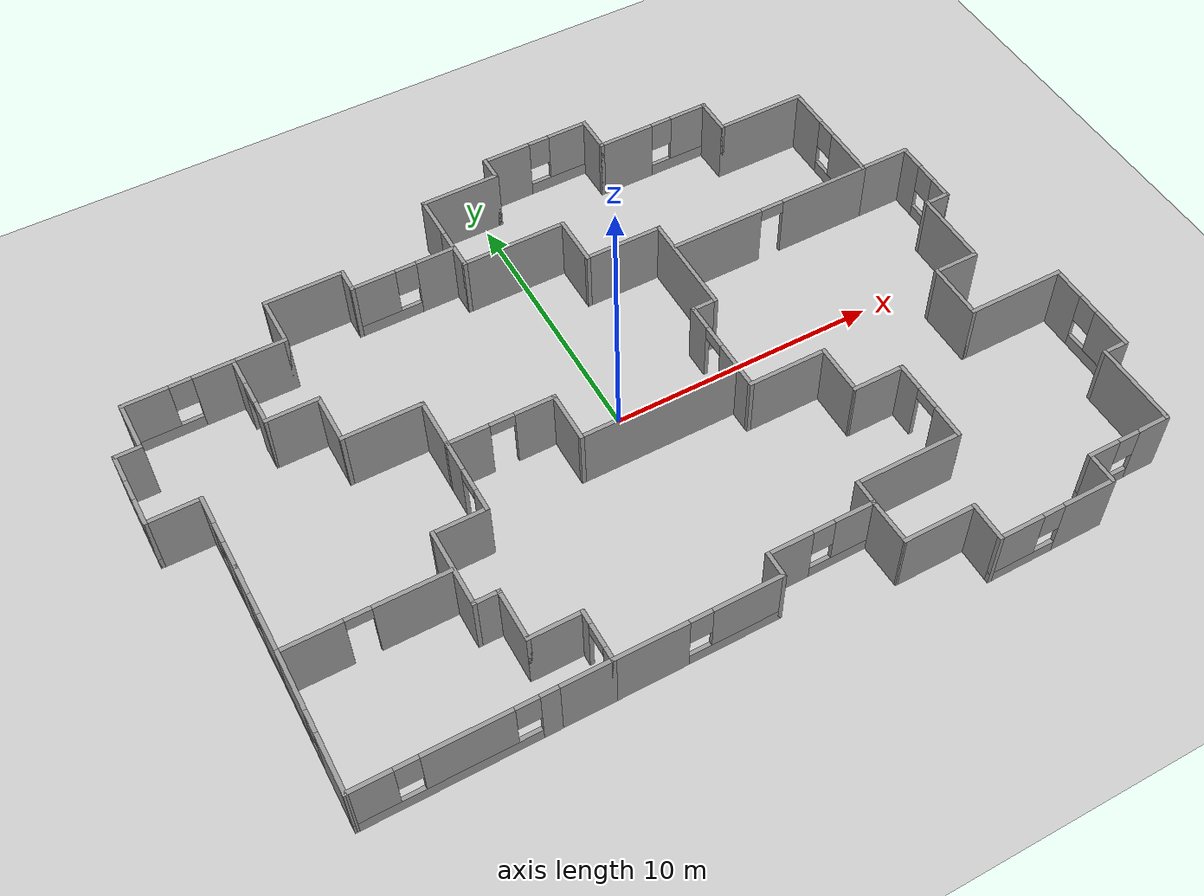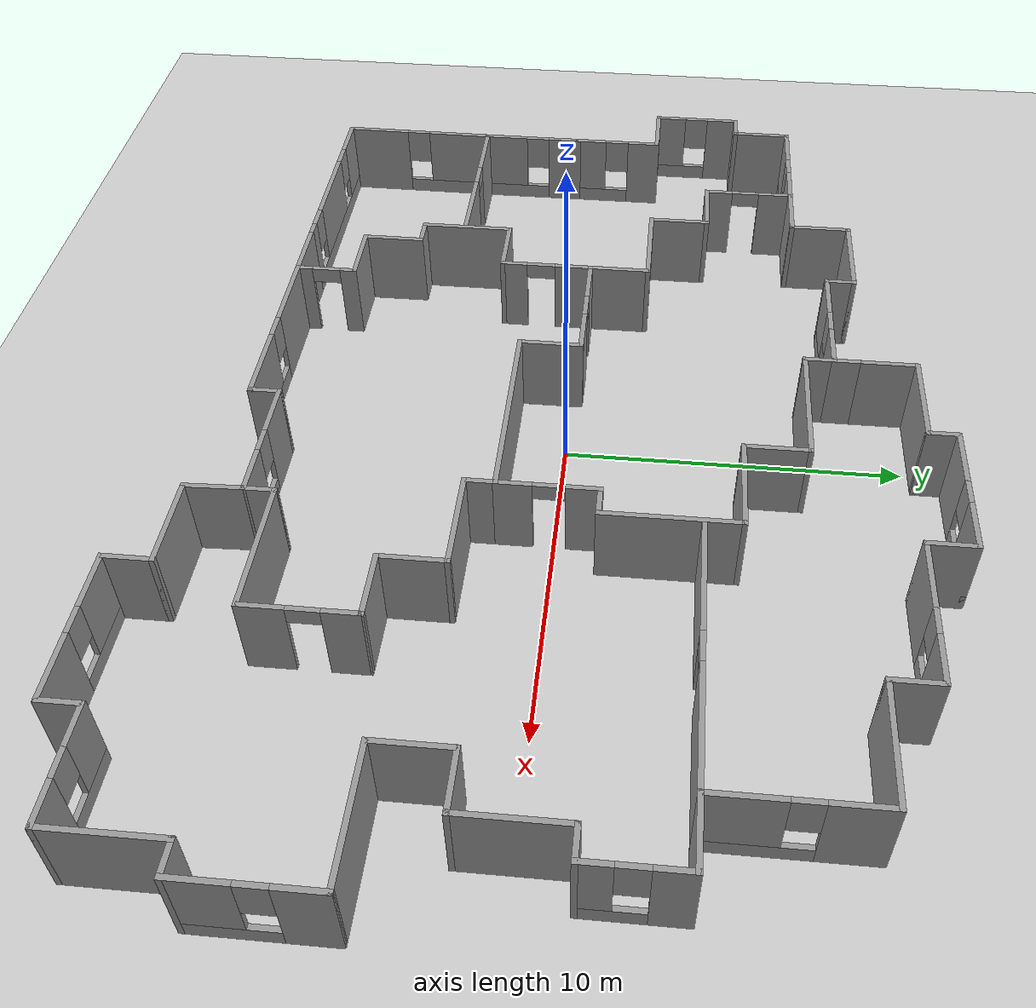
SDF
<sdf version="1.7">
 <world name="default">
  <light name="sun" type="directional">
   <pose>0 0 10 0 -0 0</pose>
   <diffuse>0.8 0.8 0.8 1</diffuse>
   <specular>0.2 0.2 0.2 1</specular>
   <attenuation>
    <range>1000</range>
    <constant>0.9</constant>
    <linear>0.01</linear>
    <quadratic>0.001</quadratic>
   </attenuation>
   <direction>-0.5 0.1 -0.9</direction>
   <spot><inner_angle>0</inner_angle><outer_angle>0</outer_angle><falloff>0</falloff></spot>
  </light>
  <model name="ground_plane">
   <static>1</static>
   <link name="link">
    <collision name="collision">
     <geometry><plane><normal>0 0 1</normal><size>100 100</size></plane></geometry>
     <surface><friction><ode><mu>100</mu><mu2>50</mu2></ode></friction></surface>
    </collision>
    <visual name="visual">
     <cast_shadows>0</cast_shadows>
     <geometry><plane><normal>0 0 1</normal><size>100 100</size></plane></geometry>
     <material>
      <script><uri>file://media/materials/scripts/gazebo.material</uri><name>Gazebo/Grey</name></script>
     </material>
    </visual>
   </link>
  </model>
  <gravity>0 0 -9.8</gravity>
  <magnetic_field>6e-06 2.3e-05 -4.2e-05</magnetic_field>
  <atmosphere type="adiabatic"/>
  <physics type="ode">
   <max_step_size>0.001</max_step_size>
   <real_time_factor>1</real_time_factor>
   <real_time_update_rate>1000</real_time_update_rate>
  </physics>
  <scene><ambient>0.4 0.4 0.4 1</ambient><background>0.7 0.7 0.7 1</background><shadows>1</shadows></scene>
  <audio><device>default</device></audio>
  <spherical_coordinates>
   <surface_model>EARTH_WGS84</surface_model>
   <latitude_deg>0</latitude_deg>
   <longitude_deg>0</longitude_deg>
   <elevation>0</elevation>
   <heading_deg>0</heading_deg>
  </spherical_coordinates>
  <model name="my_office">
   <pose>-0.02514 -0.08544 0 0 -0 0</pose>
   <link name="Wall_10">
    <collision name="Wall_10_Collision">
     <geometry><box><size>2 0.15 2.5</size></box></geometry>
     <pose>0 0 1.25 0 -0 0</pose>
    </collision>
    <visual name="Wall_10_Visual">
     <pose>0 0 1.25 0 -0 0</pose>
     <geometry><box><size>2 0.15 2.5</size></box></geometry>
     <material>
      <script><uri>file://media/materials/scripts/gazebo.material</uri><name>Gazebo/Grey</name></script>
      <ambient>1 1 1 1</ambient>
     </material>
     <meta><layer>0</layer></meta>
    </visual>
    <pose>6.5 -3.275 0 0 -0 1.5708</pose>
   </link>
   <link name="Wall_11">
    <collision name="Wall_11_Collision">
     <geometry><box><size>3 0.15 2.5</size></box></geometry>
     <pose>0 0 1.25 0 -0 0</pose>
    </collision>
    <visual name="Wall_11_Visual">
     <pose>0 0 1.25 0 -0 0</pose>
     <geometry><box><size>3 0.15 2.5</size></box></geometry>
     <material>
      <script><uri>file://media/materials/scripts/gazebo.material</uri><name>Gazebo/Grey</name></script>
      <ambient>1 1 1 1</ambient>
     </material>
     <meta><layer>0</layer></meta>
    </visual>
    <pose>5.075 -2.35 0 0 -0 3.14159</pose>
   </link>
   <link name="Wall_12">
    <collision name="Wall_12_Collision">
     <geometry><box><size>1 0.15 2.5</size></box></geometry>
     <pose>0 0 1.25 0 -0 0</pose>
    </collision>
    <visual name="Wall_12_Visual">
     <pose>0 0 1.25 0 -0 0</pose>
     <geometry><box><size>1 0.15 2.5</size></box></geometry>
     <material>
      <script><uri>file://media/materials/scripts/gazebo.material</uri><name>Gazebo/Grey</name></script>
      <ambient>1 1 1 1</ambient>
     </material>
     <meta><layer>0</layer></meta>
    </visual>
    <pose>3.65 -1.925 0 0 -0 1.5708</pose>
   </link>
   <link name="Wall_13">
    <collision name="Wall_13_Collision">
     <geometry><box><size>6 0.15 2.5</size></box></geometry>
     <pose>0 0 1.25 0 -0 0</pose>
    </collision>
    <visual name="Wall_13_Visual">
     <pose>0 0 1.25 0 -0 0</pose>
     <geometry><box><size>6 0.15 2.5</size></box></geometry>
     <material>
      <script><uri>file://media/materials/scripts/gazebo.material</uri><name>Gazebo/Grey</name></script>
      <ambient>1 1 1 1</ambient>
     </material>
     <meta><layer>0</layer></meta>
    </visual>
    <pose>0.725 -1.5 0 0 -0 3.14159</pose>
   </link>
   <link name="Wall_14">
    <collision name="Wall_14_Collision">
     <geometry><box><size>2 0.15 2.5</size></box></geometry>
     <pose>0 0 1.25 0 -0 0</pose>
    </collision>
    <visual name="Wall_14_Visual">
     <pose>0 0 1.25 0 -0 0</pose>
     <geometry><box><size>2 0.15 2.5</size></box></geometry>
     <material>
      <script><uri>file://media/materials/scripts/gazebo.material</uri><name>Gazebo/Grey</name></script>
      <ambient>1 1 1 1</ambient>
     </material>
     <meta><layer>0</layer></meta>
    </visual>
    <pose>-2.2 -0.575 0 0 -0 1.5708</pose>
   </link>
   <link name="Wall_15">
    <pose>-4.125 0.35 0 0 -0 3.14159</pose>
    <visual name="Wall_15_Visual_0">
     <pose>-1.22949 0 1.25 0 -0 0</pose>
     <geometry><box><size>1.54101 0.15 2.5</size></box></geometry>
     <material>
      <script><uri>file://media/materials/scripts/gazebo.material</uri><name>Gazebo/Grey</name></script>
      <ambient>1 1 1 1</ambient>
     </material>
     <meta><layer>0</layer></meta>
    </visual>
    <collision name="Wall_15_Collision_0">
     <geometry><box><size>1.54101 0.15 2.5</size></box></geometry>
     <pose>-1.22949 0 1.25 0 -0 0</pose>
    </collision>
    <visual name="Wall_15_Visual_1">
     <pose>1.22051 0 1.25 0 -0 0</pose>
     <geometry><box><size>1.55899 0.15 2.5</size></box></geometry>
     <material>
      <script><uri>file://media/materials/scripts/gazebo.material</uri><name>Gazebo/Grey</name></script>
      <ambient>1 1 1 1</ambient>
     </material>
     <meta><layer>0</layer></meta>
    </visual>
    <collision name="Wall_15_Collision_1">
     <geometry><box><size>1.55899 0.15 2.5</size></box></geometry>
     <pose>1.22051 0 1.25 0 -0 0</pose>
    </collision>
    <visual name="Wall_15_Visual_2">
     <pose>-0.008987 0 2.25 0 -0 0</pose>
     <geometry><box><size>0.9 0.15 0.5</size></box></geometry>
     <material>
      <script><uri>file://media/materials/scripts/gazebo.material</uri><name>Gazebo/Grey</name></script>
      <ambient>1 1 1 1</ambient>
     </material>
     <meta><layer>0</layer></meta>
    </visual>
    <collision name="Wall_15_Collision_2">
     <geometry><box><size>0.9 0.15 0.5</size></box></geometry>
     <pose>-0.008987 0 2.25 0 -0 0</pose>
    </collision>
   </link>
   <link name="Wall_16">
    <pose>-6.05 -1.075 0 0 -0 -1.5708</pose>
    <visual name="Wall_16_Visual_0">
     <pose>-0.886999 0 1.25 0 -0 0</pose>
     <geometry><box><size>1.226 0.15 2.5</size></box></geometry>
     <material>
      <script><uri>file://media/materials/scripts/gazebo.material</uri><name>Gazebo/Grey</name></script>
      <ambient>1 1 1 1</ambient>
     </material>
     <meta><layer>0</layer></meta>
    </visual>
    <collision name="Wall_16_Collision_0">
     <geometry><box><size>1.226 0.15 2.5</size></box></geometry>
     <pose>-0.886999 0 1.25 0 -0 0</pose>
    </collision>
    <visual name="Wall_16_Visual_1">
     <pose>1.063 0 1.25 0 -0 0</pose>
     <geometry><box><size>0.873997 0.15 2.5</size></box></geometry>
     <material>
      <script><uri>file://media/materials/scripts/gazebo.material</uri><name>Gazebo/Grey</name></script>
      <ambient>1 1 1 1</ambient>
     </material>
     <meta><layer>0</layer></meta>
    </visual>
    <collision name="Wall_16_Collision_1">
     <geometry><box><size>0.873997 0.15 2.5</size></box></geometry>
     <pose>1.063 0 1.25 0 -0 0</pose>
    </collision>
    <visual name="Wall_16_Visual_2">
     <pose>0.176003 0 2.25 0 -0 0</pose>
     <geometry><box><size>0.9 0.15 0.5</size></box></geometry>
     <material>
      <script><uri>file://media/materials/scripts/gazebo.material</uri><name>Gazebo/Grey</name></script>
      <ambient>1 1 1 1</ambient>
     </material>
     <meta><layer>0</layer></meta>
    </visual>
    <collision name="Wall_16_Collision_2">
     <geometry><box><size>0.9 0.15 0.5</size></box></geometry>
     <pose>0.176003 0 2.25 0 -0 0</pose>
    </collision>
   </link>
   <link name="Wall_17">
    <collision name="Wall_17_Collision">
     <geometry><box><size>2 0.15 2.5</size></box></geometry>
     <pose>0 0 1.25 0 -0 0</pose>
    </collision>
    <visual name="Wall_17_Visual">
     <pose>0 0 1.25 0 -0 0</pose>
     <geometry><box><size>2 0.15 2.5</size></box></geometry>
     <material>
      <script><uri>file://media/materials/scripts/gazebo.material</uri><name>Gazebo/Grey</name></script>
      <ambient>1 1 1 1</ambient>
     </material>
     <meta><layer>0</layer></meta>
    </visual>
    <pose>-6.975 -2.5 0 0 -0 3.14159</pose>
   </link>
   <link name="Wall_18">
    <collision name="Wall_18_Collision">
     <geometry><box><size>3 0.15 2.5</size></box></geometry>
     <pose>0 0 1.25 0 -0 0</pose>
    </collision>
    <visual name="Wall_18_Visual">
     <pose>0 0 1.25 0 -0 0</pose>
     <geometry><box><size>3 0.15 2.5</size></box></geometry>
     <material>
      <script><uri>file://media/materials/scripts/gazebo.material</uri><name>Gazebo/Grey</name></script>
      <ambient>1 1 1 1</ambient>
     </material>
     <meta><layer>0</layer></meta>
    </visual>
    <pose>-7.9 -3.925 0 0 -0 -1.5708</pose>
   </link>
   <link name="Wall_19">
    <collision name="Wall_19_Collision">
     <geometry><box><size>1 0.15 2.5</size></box></geometry>
     <pose>0 0 1.25 0 -0 0</pose>
    </collision>
    <visual name="Wall_19_Visual">
     <pose>0 0 1.25 0 -0 0</pose>
     <geometry><box><size>1 0.15 2.5</size></box></geometry>
     <material>
      <script><uri>file://media/materials/scripts/gazebo.material</uri><name>Gazebo/Grey</name></script>
      <ambient>1 1 1 1</ambient>
     </material>
     <meta><layer>0</layer></meta>
    </visual>
    <pose>-7.475 -5.35 0 0 -0 0</pose>
   </link>
   <link name="Wall_20">
    <collision name="Wall_20_Collision">
     <geometry><box><size>2 0.15 2.5</size></box></geometry>
     <pose>0 0 1.25 0 -0 0</pose>
    </collision>
    <visual name="Wall_20_Visual">
     <pose>0 0 1.25 0 -0 0</pose>
     <geometry><box><size>2 0.15 2.5</size></box></geometry>
     <material>
      <script><uri>file://media/materials/scripts/gazebo.material</uri><name>Gazebo/Grey</name></script>
      <ambient>1 1 1 1</ambient>
     </material>
     <meta><layer>0</layer></meta>
    </visual>
    <pose>-7.05 -6.275 0 0 -0 -1.5708</pose>
   </link>
   <link name="Wall_21">
    <collision name="Wall_21_Collision">
     <geometry><box><size>2 0.15 2.5</size></box></geometry>
     <pose>0 0 1.25 0 -0 0</pose>
    </collision>
    <visual name="Wall_21_Visual">
     <pose>0 0 1.25 0 -0 0</pose>
     <geometry><box><size>2 0.15 2.5</size></box></geometry>
     <material>
      <script><uri>file://media/materials/scripts/gazebo.material</uri><name>Gazebo/Grey</name></script>
      <ambient>1 1 1 1</ambient>
     </material>
     <meta><layer>0</layer></meta>
    </visual>
    <pose>-6.125 -7.2 0 0 -0 0</pose>
   </link>
   <link name="Wall_22">
    <pose>-5.2 -8.125 0 0 -0 -1.5708</pose>
    <visual name="Wall_22_Visual_0">
     <pose>-0.728709 0 1.25 0 -0 0</pose>
     <geometry><box><size>0.542581 0.15 2.5</size></box></geometry>
     <material>
      <script><uri>file://media/materials/scripts/gazebo.material</uri><name>Gazebo/Grey</name></script>
      <ambient>1 1 1 1</ambient>
     </material>
     <meta><layer>0</layer></meta>
    </visual>
    <collision name="Wall_22_Collision_0">
     <geometry><box><size>0.542581 0.15 2.5</size></box></geometry>
     <pose>-0.728709 0 1.25 0 -0 0</pose>
    </collision>
    <visual name="Wall_22_Visual_1">
     <pose>0.721291 0 1.25 0 -0 0</pose>
     <geometry><box><size>0.557419 0.15 2.5</size></box></geometry>
     <material>
      <script><uri>file://media/materials/scripts/gazebo.material</uri><name>Gazebo/Grey</name></script>
      <ambient>1 1 1 1</ambient>
     </material>
     <meta><layer>0</layer></meta>
    </visual>
    <collision name="Wall_22_Collision_1">
     <geometry><box><size>0.557419 0.15 2.5</size></box></geometry>
     <pose>0.721291 0 1.25 0 -0 0</pose>
    </collision>
    <visual name="Wall_22_Visual_2">
     <pose>-0.007419 0 2.25 0 -0 0</pose>
     <geometry><box><size>0.9 0.15 0.5</size></box></geometry>
     <material>
      <script><uri>file://media/materials/scripts/gazebo.material</uri><name>Gazebo/Grey</name></script>
      <ambient>1 1 1 1</ambient>
     </material>
     <meta><layer>0</layer></meta>
    </visual>
    <collision name="Wall_22_Collision_2">
     <geometry><box><size>0.9 0.15 0.5</size></box></geometry>
     <pose>-0.007419 0 2.25 0 -0 0</pose>
    </collision>
   </link>
   <link name="Wall_23">
    <pose>-2.275 -9.05 0 0 -0 0</pose>
    <visual name="Wall_23_Visual_0">
     <pose>-1.67725 0 1.25 0 -0 0</pose>
     <geometry><box><size>2.6455 0.15 2.5</size></box></geometry>
     <material>
      <script><uri>file://media/materials/scripts/gazebo.material</uri><name>Gazebo/Grey</name></script>
      <ambient>1 1 1 1</ambient>
     </material>
     <meta><layer>0</layer></meta>
    </visual>
    <collision name="Wall_23_Collision_0">
     <geometry><box><size>2.6455 0.15 2.5</size></box></geometry>
     <pose>-1.67725 0 1.25 0 -0 0</pose>
    </collision>
    <visual name="Wall_23_Visual_1">
     <pose>1.32275 0 0.25 0 -0 0</pose>
     <geometry><box><size>3.3545 0.15 0.5</size></box></geometry>
     <material>
      <script><uri>file://media/materials/scripts/gazebo.material</uri><name>Gazebo/Grey</name></script>
      <ambient>1 1 1 1</ambient>
     </material>
     <meta><layer>0</layer></meta>
    </visual>
    <collision name="Wall_23_Collision_1">
     <geometry><box><size>3.3545 0.15 0.5</size></box></geometry>
     <pose>1.32275 0 0.25 0 -0 0</pose>
    </collision>
    <visual name="Wall_23_Visual_2">
     <pose>1.72275 0 1.5 0 -0 0</pose>
     <geometry><box><size>2.5545 0.15 2</size></box></geometry>
     <material>
      <script><uri>file://media/materials/scripts/gazebo.material</uri><name>Gazebo/Grey</name></script>
      <ambient>1 1 1 1</ambient>
     </material>
     <meta><layer>0</layer></meta>
    </visual>
    <collision name="Wall_23_Collision_2">
     <geometry><box><size>2.5545 0.15 2</size></box></geometry>
     <pose>1.72275 0 1.5 0 -0 0</pose>
    </collision>
    <visual name="Wall_23_Visual_3">
     <pose>0.045496 0 1.9 0 -0 0</pose>
     <geometry><box><size>0.8 0.15 1.2</size></box></geometry>
     <material>
      <script><uri>file://media/materials/scripts/gazebo.material</uri><name>Gazebo/Grey</name></script>
      <ambient>1 1 1 1</ambient>
     </material>
     <meta><layer>0</layer></meta>
    </visual>
    <collision name="Wall_23_Collision_3">
     <geometry><box><size>0.8 0.15 1.2</size></box></geometry>
     <pose>0.045496 0 1.9 0 -0 0</pose>
    </collision>
   </link>
   <link name="Wall_24">
    <collision name="Wall_24_Collision">
     <geometry><box><size>1 0.15 2.5</size></box></geometry>
     <pose>0 0 1.25 0 -0 0</pose>
    </collision>
    <visual name="Wall_24_Visual">
     <pose>0 0 1.25 0 -0 0</pose>
     <geometry><box><size>1 0.15 2.5</size></box></geometry>
     <material>
      <script><uri>file://media/materials/scripts/gazebo.material</uri><name>Gazebo/Grey</name></script>
      <ambient>1 1 1 1</ambient>
     </material>
     <meta><layer>0</layer></meta>
    </visual>
    <pose>0.65 -8.625 0 0 -0 1.5708</pose>
   </link>
   <link name="Wall_25">
    <pose>2.575 -8.2 0 0 -0 0</pose>
    <visual name="Wall_25_Visual_0">
     <pose>-1.15778 0 1.25 0 -0 0</pose>
     <geometry><box><size>1.68443 0.15 2.5</size></box></geometry>
     <material>
      <script><uri>file://media/materials/scripts/gazebo.material</uri><name>Gazebo/Grey</name></script>
      <ambient>1 1 1 1</ambient>
     </material>
     <meta><layer>0</layer></meta>
    </visual>
    <collision name="Wall_25_Collision_0">
     <geometry><box><size>1.68443 0.15 2.5</size></box></geometry>
     <pose>-1.15778 0 1.25 0 -0 0</pose>
    </collision>
    <visual name="Wall_25_Visual_1">
     <pose>0.842216 0 0.25 0 -0 0</pose>
     <geometry><box><size>2.31557 0.15 0.5</size></box></geometry>
     <material>
      <script><uri>file://media/materials/scripts/gazebo.material</uri><name>Gazebo/Grey</name></script>
      <ambient>1 1 1 1</ambient>
     </material>
     <meta><layer>0</layer></meta>
    </visual>
    <collision name="Wall_25_Collision_1">
     <geometry><box><size>2.31557 0.15 0.5</size></box></geometry>
     <pose>0.842216 0 0.25 0 -0 0</pose>
    </collision>
    <visual name="Wall_25_Visual_2">
     <pose>1.24222 0 1.5 0 -0 0</pose>
     <geometry><box><size>1.51557 0.15 2</size></box></geometry>
     <material>
      <script><uri>file://media/materials/scripts/gazebo.material</uri><name>Gazebo/Grey</name></script>
      <ambient>1 1 1 1</ambient>
     </material>
     <meta><layer>0</layer></meta>
    </visual>
    <collision name="Wall_25_Collision_2">
     <geometry><box><size>1.51557 0.15 2</size></box></geometry>
     <pose>1.24222 0 1.5 0 -0 0</pose>
    </collision>
    <visual name="Wall_25_Visual_3">
     <pose>0.084432 0 1.9 0 -0 0</pose>
     <geometry><box><size>0.8 0.15 1.2</size></box></geometry>
     <material>
      <script><uri>file://media/materials/scripts/gazebo.material</uri><name>Gazebo/Grey</name></script>
      <ambient>1 1 1 1</ambient>
     </material>
     <meta><layer>0</layer></meta>
    </visual>
    <collision name="Wall_25_Collision_3">
     <geometry><box><size>0.8 0.15 1.2</size></box></geometry>
     <pose>0.084432 0 1.9 0 -0 0</pose>
    </collision>
   </link>
   <link name="Wall_26">
    <collision name="Wall_26_Collision">
     <geometry><box><size>1 0.15 2.5</size></box></geometry>
     <pose>0 0 1.25 0 -0 0</pose>
    </collision>
    <visual name="Wall_26_Visual">
     <pose>0 0 1.25 0 -0 0</pose>
     <geometry><box><size>1 0.15 2.5</size></box></geometry>
     <material>
      <script><uri>file://media/materials/scripts/gazebo.material</uri><name>Gazebo/Grey</name></script>
      <ambient>1 1 1 1</ambient>
     </material>
     <meta><layer>0</layer></meta>
    </visual>
    <pose>4.5 -7.775 0 0 -0 1.5708</pose>
   </link>
   <link name="Wall_27">
    <collision name="Wall_27_Collision">
     <geometry><box><size>4 0.15 2.5</size></box></geometry>
     <pose>0 0 1.25 0 -0 0</pose>
    </collision>
    <visual name="Wall_27_Visual">
     <pose>0 0 1.25 0 -0 0</pose>
     <geometry><box><size>4 0.15 2.5</size></box></geometry>
     <material>
      <script><uri>file://media/materials/scripts/gazebo.material</uri><name>Gazebo/Grey</name></script>
      <ambient>1 1 1 1</ambient>
     </material>
     <meta><layer>0</layer></meta>
    </visual>
    <pose>6.425 -7.35 0 0 -0 0</pose>
   </link>
   <link name="Wall_29">
    <collision name="Wall_29_Collision">
     <geometry><box><size>2 0.15 2.5</size></box></geometry>
     <pose>0 0 1.25 0 -0 0</pose>
    </collision>
    <visual name="Wall_29_Visual">
     <pose>0 0 1.25 0 -0 0</pose>
     <geometry><box><size>2 0.15 2.5</size></box></geometry>
     <material>
      <script><uri>file://media/materials/scripts/gazebo.material</uri><name>Gazebo/Grey</name></script>
      <ambient>1 1 1 1</ambient>
     </material>
     <meta><layer>0</layer></meta>
    </visual>
    <pose>-6.05 1.275 0 0 -0 1.5708</pose>
   </link>
   <link name="Wall_30">
    <collision name="Wall_30_Collision">
     <geometry><box><size>3 0.15 2.5</size></box></geometry>
     <pose>0 0 1.25 0 -0 0</pose>
    </collision>
    <visual name="Wall_30_Visual">
     <pose>0 0 1.25 0 -0 0</pose>
     <geometry><box><size>3 0.15 2.5</size></box></geometry>
     <material>
      <script><uri>file://media/materials/scripts/gazebo.material</uri><name>Gazebo/Grey</name></script>
      <ambient>1 1 1 1</ambient>
     </material>
     <meta><layer>0</layer></meta>
    </visual>
    <pose>-7.475 2.2 0 0 -0 3.14159</pose>
   </link>
   <link name="Wall_31">
    <collision name="Wall_31_Collision">
     <geometry><box><size>2 0.15 2.5</size></box></geometry>
     <pose>0 0 1.25 0 -0 0</pose>
    </collision>
    <visual name="Wall_31_Visual">
     <pose>0 0 1.25 0 -0 0</pose>
     <geometry><box><size>2 0.15 2.5</size></box></geometry>
     <material>
      <script><uri>file://media/materials/scripts/gazebo.material</uri><name>Gazebo/Grey</name></script>
      <ambient>1 1 1 1</ambient>
     </material>
     <meta><layer>0</layer></meta>
    </visual>
    <pose>-8.9 3.125 0 0 -0 1.5708</pose>
   </link>
   <link name="Wall_34">
    <collision name="Wall_34_Collision">
     <geometry><box><size>2 0.15 2.5</size></box></geometry>
     <pose>0 0 1.25 0 -0 0</pose>
    </collision>
    <visual name="Wall_34_Visual">
     <pose>0 0 1.25 0 -0 0</pose>
     <geometry><box><size>2 0.15 2.5</size></box></geometry>
     <material>
      <script><uri>file://media/materials/scripts/gazebo.material</uri><name>Gazebo/Grey</name></script>
      <ambient>1 1 1 1</ambient>
     </material>
     <meta><layer>0</layer></meta>
    </visual>
    <pose>-9.825 4.05 0 0 -0 3.14159</pose>
   </link>
   <link name="Wall_35">
    <pose>-10.75 5.475 0 0 -0 1.5708</pose>
    <visual name="Wall_35_Visual_0">
     <pose>-1.02718 0 1.25 0 -0 0</pose>
     <geometry><box><size>0.945638 0.15 2.5</size></box></geometry>
     <material>
      <script><uri>file://media/materials/scripts/gazebo.material</uri><name>Gazebo/Grey</name></script>
      <ambient>1 1 1 1</ambient>
     </material>
     <meta><layer>0</layer></meta>
    </visual>
    <collision name="Wall_35_Collision_0">
     <geometry><box><size>0.945638 0.15 2.5</size></box></geometry>
     <pose>-1.02718 0 1.25 0 -0 0</pose>
    </collision>
    <visual name="Wall_35_Visual_1">
     <pose>0.922819 0 1.25 0 -0 0</pose>
     <geometry><box><size>1.15436 0.15 2.5</size></box></geometry>
     <material>
      <script><uri>file://media/materials/scripts/gazebo.material</uri><name>Gazebo/Grey</name></script>
      <ambient>1 1 1 1</ambient>
     </material>
     <meta><layer>0</layer></meta>
    </visual>
    <collision name="Wall_35_Collision_1">
     <geometry><box><size>1.15436 0.15 2.5</size></box></geometry>
     <pose>0.922819 0 1.25 0 -0 0</pose>
    </collision>
    <visual name="Wall_35_Visual_2">
     <pose>-0.104362 0 2.25 0 -0 0</pose>
     <geometry><box><size>0.9 0.15 0.5</size></box></geometry>
     <material>
      <script><uri>file://media/materials/scripts/gazebo.material</uri><name>Gazebo/Grey</name></script>
      <ambient>1 1 1 1</ambient>
     </material>
     <meta><layer>0</layer></meta>
    </visual>
    <collision name="Wall_35_Collision_2">
     <geometry><box><size>0.9 0.15 0.5</size></box></geometry>
     <pose>-0.104362 0 2.25 0 -0 0</pose>
    </collision>
   </link>
   <link name="Wall_36">
    <collision name="Wall_36_Collision">
     <geometry><box><size>2 0.15 2.5</size></box></geometry>
     <pose>0 0 1.25 0 -0 0</pose>
    </collision>
    <visual name="Wall_36_Visual">
     <pose>0 0 1.25 0 -0 0</pose>
     <geometry><box><size>2 0.15 2.5</size></box></geometry>
     <material>
      <script><uri>file://media/materials/scripts/gazebo.material</uri><name>Gazebo/Grey</name></script>
      <ambient>1 1 1 1</ambient>
     </material>
     <meta><layer>0</layer></meta>
    </visual>
    <pose>-9.825 6.9 0 0 -0 0</pose>
   </link>
   <link name="Wall_38">
    <pose>3.65 -0.075 0 0 -0 1.5708</pose>
    <visual name="Wall_38_Visual_0">
     <pose>-0.960473 0 1.25 0 -0 0</pose>
     <geometry><box><size>1.07906 0.15 2.5</size></box></geometry>
     <material>
      <script><uri>file://media/materials/scripts/gazebo.material</uri><name>Gazebo/Grey</name></script>
      <ambient>1 1 1 1</ambient>
     </material>
     <meta><layer>0</layer></meta>
    </visual>
    <collision name="Wall_38_Collision_0">
     <geometry><box><size>1.07906 0.15 2.5</size></box></geometry>
     <pose>-0.960473 0 1.25 0 -0 0</pose>
    </collision>
    <visual name="Wall_38_Visual_1">
     <pose>0.989527 0 1.25 0 -0 0</pose>
     <geometry><box><size>1.02094 0.15 2.5</size></box></geometry>
     <material>
      <script><uri>file://media/materials/scripts/gazebo.material</uri><name>Gazebo/Grey</name></script>
      <ambient>1 1 1 1</ambient>
     </material>
     <meta><layer>0</layer></meta>
    </visual>
    <collision name="Wall_38_Collision_1">
     <geometry><box><size>1.02094 0.15 2.5</size></box></geometry>
     <pose>0.989527 0 1.25 0 -0 0</pose>
    </collision>
    <visual name="Wall_38_Visual_2">
     <pose>0.029055 0 2.25 0 -0 0</pose>
     <geometry><box><size>0.9 0.15 0.5</size></box></geometry>
     <material>
      <script><uri>file://media/materials/scripts/gazebo.material</uri><name>Gazebo/Grey</name></script>
      <ambient>1 1 1 1</ambient>
     </material>
     <meta><layer>0</layer></meta>
    </visual>
    <collision name="Wall_38_Collision_2">
     <geometry><box><size>0.9 0.15 0.5</size></box></geometry>
     <pose>0.029055 0 2.25 0 -0 0</pose>
    </collision>
   </link>
   <link name="Wall_39">
    <collision name="Wall_39_Collision">
     <geometry><box><size>1 0.15 2.5</size></box></geometry>
     <pose>0 0 1.25 0 -0 0</pose>
    </collision>
    <visual name="Wall_39_Visual">
     <pose>0 0 1.25 0 -0 0</pose>
     <geometry><box><size>1 0.15 2.5</size></box></geometry>
     <material>
      <script><uri>file://media/materials/scripts/gazebo.material</uri><name>Gazebo/Grey</name></script>
      <ambient>1 1 1 1</ambient>
     </material>
     <meta><layer>0</layer></meta>
    </visual>
    <pose>4.075 1.35 0 0 -0 0</pose>
   </link>
   <link name="Wall_40">
    <collision name="Wall_40_Collision">
     <geometry><box><size>4 0.15 2.5</size></box></geometry>
     <pose>0 0 1.25 0 -0 0</pose>
    </collision>
    <visual name="Wall_40_Visual">
     <pose>0 0 1.25 0 -0 0</pose>
     <geometry><box><size>4 0.15 2.5</size></box></geometry>
     <material>
      <script><uri>file://media/materials/scripts/gazebo.material</uri><name>Gazebo/Grey</name></script>
      <ambient>1 1 1 1</ambient>
     </material>
     <meta><layer>0</layer></meta>
    </visual>
    <pose>4.5 3.275 0 0 -0 1.5708</pose>
   </link>
   <link name="Wall_41">
    <collision name="Wall_41_Collision">
     <geometry><box><size>3 0.15 2.5</size></box></geometry>
     <pose>0 0 1.25 0 -0 0</pose>
    </collision>
    <visual name="Wall_41_Visual">
     <pose>0 0 1.25 0 -0 0</pose>
     <geometry><box><size>3 0.15 2.5</size></box></geometry>
     <material>
      <script><uri>file://media/materials/scripts/gazebo.material</uri><name>Gazebo/Grey</name></script>
      <ambient>1 1 1 1</ambient>
     </material>
     <meta><layer>0</layer></meta>
    </visual>
    <pose>3.075 5.2 0 0 -0 3.14159</pose>
   </link>
   <link name="Wall_42">
    <collision name="Wall_42_Collision">
     <geometry><box><size>2 0.15 2.5</size></box></geometry>
     <pose>0 0 1.25 0 -0 0</pose>
    </collision>
    <visual name="Wall_42_Visual">
     <pose>0 0 1.25 0 -0 0</pose>
     <geometry><box><size>2 0.15 2.5</size></box></geometry>
     <material>
      <script><uri>file://media/materials/scripts/gazebo.material</uri><name>Gazebo/Grey</name></script>
      <ambient>1 1 1 1</ambient>
     </material>
     <meta><layer>0</layer></meta>
    </visual>
    <pose>1.65 6.125 0 0 -0 1.5708</pose>
   </link>
   <link name="Wall_43">
    <collision name="Wall_43_Collision">
     <geometry><box><size>4 0.15 2.5</size></box></geometry>
     <pose>0 0 1.25 0 -0 0</pose>
    </collision>
    <visual name="Wall_43_Visual">
     <pose>0 0 1.25 0 -0 0</pose>
     <geometry><box><size>4 0.15 2.5</size></box></geometry>
     <material>
      <script><uri>file://media/materials/scripts/gazebo.material</uri><name>Gazebo/Grey</name></script>
      <ambient>1 1 1 1</ambient>
     </material>
     <meta><layer>0</layer></meta>
    </visual>
    <pose>-0.275 7.05 0 0 -0 3.14159</pose>
   </link>
   <link name="Wall_45">
    <collision name="Wall_45_Collision">
     <geometry><box><size>1 0.15 2.5</size></box></geometry>
     <pose>0 0 1.25 0 -0 0</pose>
    </collision>
    <visual name="Wall_45_Visual">
     <pose>0 0 1.25 0 -0 0</pose>
     <geometry><box><size>1 0.15 2.5</size></box></geometry>
     <material>
      <script><uri>file://media/materials/scripts/gazebo.material</uri><name>Gazebo/Grey</name></script>
      <ambient>1 1 1 1</ambient>
     </material>
     <meta><layer>0</layer></meta>
    </visual>
    <pose>-2.2 7.475 0 0 -0 1.5708</pose>
   </link>
   <link name="Wall_46">
    <pose>-4.125 7.9 0 0 -0 3.14159</pose>
    <visual name="Wall_46_Visual_0">
     <pose>-1.23202 0 1.25 0 -0 0</pose>
     <geometry><box><size>1.53595 0.15 2.5</size></box></geometry>
     <material>
      <script><uri>file://media/materials/scripts/gazebo.material</uri><name>Gazebo/Grey</name></script>
      <ambient>1 1 1 1</ambient>
     </material>
     <meta><layer>0</layer></meta>
    </visual>
    <collision name="Wall_46_Collision_0">
     <geometry><box><size>1.53595 0.15 2.5</size></box></geometry>
     <pose>-1.23202 0 1.25 0 -0 0</pose>
    </collision>
    <visual name="Wall_46_Visual_1">
     <pose>0.767977 0 0.25 0 -0 0</pose>
     <geometry><box><size>2.46405 0.15 0.5</size></box></geometry>
     <material>
      <script><uri>file://media/materials/scripts/gazebo.material</uri><name>Gazebo/Grey</name></script>
      <ambient>1 1 1 1</ambient>
     </material>
     <meta><layer>0</layer></meta>
    </visual>
    <collision name="Wall_46_Collision_1">
     <geometry><box><size>2.46405 0.15 0.5</size></box></geometry>
     <pose>0.767977 0 0.25 0 -0 0</pose>
    </collision>
    <visual name="Wall_46_Visual_2">
     <pose>1.16798 0 1.5 0 -0 0</pose>
     <geometry><box><size>1.66405 0.15 2</size></box></geometry>
     <material>
      <script><uri>file://media/materials/scripts/gazebo.material</uri><name>Gazebo/Grey</name></script>
      <ambient>1 1 1 1</ambient>
     </material>
     <meta><layer>0</layer></meta>
    </visual>
    <collision name="Wall_46_Collision_2">
     <geometry><box><size>1.66405 0.15 2</size></box></geometry>
     <pose>1.16798 0 1.5 0 -0 0</pose>
    </collision>
    <visual name="Wall_46_Visual_3">
     <pose>-0.064046 0 1.9 0 -0 0</pose>
     <geometry><box><size>0.8 0.15 1.2</size></box></geometry>
     <material>
      <script><uri>file://media/materials/scripts/gazebo.material</uri><name>Gazebo/Grey</name></script>
      <ambient>1 1 1 1</ambient>
     </material>
     <meta><layer>0</layer></meta>
    </visual>
    <collision name="Wall_46_Collision_3">
     <geometry><box><size>0.8 0.15 1.2</size></box></geometry>
     <pose>-0.064046 0 1.9 0 -0 0</pose>
    </collision>
   </link>
   <link name="Wall_47">
    <collision name="Wall_47_Collision">
     <geometry><box><size>1 0.15 2.5</size></box></geometry>
     <pose>0 0 1.25 0 -0 0</pose>
    </collision>
    <visual name="Wall_47_Visual">
     <pose>0 0 1.25 0 -0 0</pose>
     <geometry><box><size>1 0.15 2.5</size></box></geometry>
     <material>
      <script><uri>file://media/materials/scripts/gazebo.material</uri><name>Gazebo/Grey</name></script>
      <ambient>1 1 1 1</ambient>
     </material>
     <meta><layer>0</layer></meta>
    </visual>
    <pose>-6.05 8.325 0 0 -0 1.5708</pose>
   </link>
   <link name="Wall_48">
    <collision name="Wall_48_Collision">
     <geometry><box><size>3 0.15 2.5</size></box></geometry>
     <pose>0 0 1.25 0 -0 0</pose>
    </collision>
    <visual name="Wall_48_Visual">
     <pose>0 0 1.25 0 -0 0</pose>
     <geometry><box><size>3 0.15 2.5</size></box></geometry>
     <material>
      <script><uri>file://media/materials/scripts/gazebo.material</uri><name>Gazebo/Grey</name></script>
      <ambient>1 1 1 1</ambient>
     </material>
     <meta><layer>0</layer></meta>
    </visual>
    <pose>-7.475 8.75 0 0 -0 3.14159</pose>
   </link>
   <link name="Wall_49">
    <collision name="Wall_49_Collision">
     <geometry><box><size>2 0.15 2.5</size></box></geometry>
     <pose>0 0 1.25 0 -0 0</pose>
    </collision>
    <visual name="Wall_49_Visual">
     <pose>0 0 1.25 0 -0 0</pose>
     <geometry><box><size>2 0.15 2.5</size></box></geometry>
     <material>
      <script><uri>file://media/materials/scripts/gazebo.material</uri><name>Gazebo/Grey</name></script>
      <ambient>1 1 1 1</ambient>
     </material>
     <meta><layer>0</layer></meta>
    </visual>
    <pose>-8.9 7.825 0 0 -0 -1.5708</pose>
   </link>
   <link name="Wall_52">
    <pose>-12.675 6.9 0 0 -0 3.14159</pose>
    <visual name="Wall_52_Visual_0">
     <pose>-1.23889 0 1.25 0 -0 0</pose>
     <geometry><box><size>1.52222 0.15 2.5</size></box></geometry>
     <material>
      <script><uri>file://media/materials/scripts/gazebo.material</uri><name>Gazebo/Grey</name></script>
      <ambient>1 1 1 1</ambient>
     </material>
     <meta><layer>0</layer></meta>
    </visual>
    <collision name="Wall_52_Collision_0">
     <geometry><box><size>1.52222 0.15 2.5</size></box></geometry>
     <pose>-1.23889 0 1.25 0 -0 0</pose>
    </collision>
    <visual name="Wall_52_Visual_1">
     <pose>0.761108 0 0.25 0 -0 0</pose>
     <geometry><box><size>2.47778 0.15 0.5</size></box></geometry>
     <material>
      <script><uri>file://media/materials/scripts/gazebo.material</uri><name>Gazebo/Grey</name></script>
      <ambient>1 1 1 1</ambient>
     </material>
     <meta><layer>0</layer></meta>
    </visual>
    <collision name="Wall_52_Collision_1">
     <geometry><box><size>2.47778 0.15 0.5</size></box></geometry>
     <pose>0.761108 0 0.25 0 -0 0</pose>
    </collision>
    <visual name="Wall_52_Visual_2">
     <pose>1.16111 0 1.5 0 -0 0</pose>
     <geometry><box><size>1.67779 0.15 2</size></box></geometry>
     <material>
      <script><uri>file://media/materials/scripts/gazebo.material</uri><name>Gazebo/Grey</name></script>
      <ambient>1 1 1 1</ambient>
     </material>
     <meta><layer>0</layer></meta>
    </visual>
    <collision name="Wall_52_Collision_2">
     <geometry><box><size>1.67779 0.15 2</size></box></geometry>
     <pose>1.16111 0 1.5 0 -0 0</pose>
    </collision>
    <visual name="Wall_52_Visual_3">
     <pose>-0.077785 0 1.9 0 -0 0</pose>
     <geometry><box><size>0.8 0.15 1.2</size></box></geometry>
     <material>
      <script><uri>file://media/materials/scripts/gazebo.material</uri><name>Gazebo/Grey</name></script>
      <ambient>1 1 1 1</ambient>
     </material>
     <meta><layer>0</layer></meta>
    </visual>
    <collision name="Wall_52_Collision_3">
     <geometry><box><size>0.8 0.15 1.2</size></box></geometry>
     <pose>-0.077785 0 1.9 0 -0 0</pose>
    </collision>
   </link>
   <link name="Wall_54">
    <collision name="Wall_54_Collision">
     <geometry><box><size>2 0.15 2.5</size></box></geometry>
     <pose>0 0 1.25 0 -0 0</pose>
    </collision>
    <visual name="Wall_54_Visual">
     <pose>0 0 1.25 0 -0 0</pose>
     <geometry><box><size>2 0.15 2.5</size></box></geometry>
     <material>
      <script><uri>file://media/materials/scripts/gazebo.material</uri><name>Gazebo/Grey</name></script>
      <ambient>1 1 1 1</ambient>
     </material>
     <meta><layer>0</layer></meta>
    </visual>
    <pose>-14.6 5.975 0 0 -0 -1.5708</pose>
   </link>
   <link name="Wall_55">
    <collision name="Wall_55_Collision">
     <geometry><box><size>1 0.15 2.5</size></box></geometry>
     <pose>0 0 1.25 0 -0 0</pose>
    </collision>
    <visual name="Wall_55_Visual">
     <pose>0 0 1.25 0 -0 0</pose>
     <geometry><box><size>1 0.15 2.5</size></box></geometry>
     <material>
      <script><uri>file://media/materials/scripts/gazebo.material</uri><name>Gazebo/Grey</name></script>
      <ambient>1 1 1 1</ambient>
     </material>
     <meta><layer>0</layer></meta>
    </visual>
    <pose>-15.025 5.05 0 0 -0 3.14159</pose>
   </link>
   <link name="Wall_56">
    <pose>-15.45 3.625 0 0 -0 -1.5708</pose>
    <visual name="Wall_56_Visual_0">
     <pose>-0.941289 0 1.25 0 -0 0</pose>
     <geometry><box><size>1.11742 0.15 2.5</size></box></geometry>
     <material>
      <script><uri>file://media/materials/scripts/gazebo.material</uri><name>Gazebo/Grey</name></script>
      <ambient>1 1 1 1</ambient>
     </material>
     <meta><layer>0</layer></meta>
    </visual>
    <collision name="Wall_56_Collision_0">
     <geometry><box><size>1.11742 0.15 2.5</size></box></geometry>
     <pose>-0.941289 0 1.25 0 -0 0</pose>
    </collision>
    <visual name="Wall_56_Visual_1">
     <pose>0.558711 0 0.25 0 -0 0</pose>
     <geometry><box><size>1.88258 0.15 0.5</size></box></geometry>
     <material>
      <script><uri>file://media/materials/scripts/gazebo.material</uri><name>Gazebo/Grey</name></script>
      <ambient>1 1 1 1</ambient>
     </material>
     <meta><layer>0</layer></meta>
    </visual>
    <collision name="Wall_56_Collision_1">
     <geometry><box><size>1.88258 0.15 0.5</size></box></geometry>
     <pose>0.558711 0 0.25 0 -0 0</pose>
    </collision>
    <visual name="Wall_56_Visual_2">
     <pose>0.958711 0 1.5 0 -0 0</pose>
     <geometry><box><size>1.08258 0.15 2</size></box></geometry>
     <material>
      <script><uri>file://media/materials/scripts/gazebo.material</uri><name>Gazebo/Grey</name></script>
      <ambient>1 1 1 1</ambient>
     </material>
     <meta><layer>0</layer></meta>
    </visual>
    <collision name="Wall_56_Collision_2">
     <geometry><box><size>1.08258 0.15 2</size></box></geometry>
     <pose>0.958711 0 1.5 0 -0 0</pose>
    </collision>
    <visual name="Wall_56_Visual_3">
     <pose>0.017422 0 1.9 0 -0 0</pose>
     <geometry><box><size>0.8 0.15 1.2</size></box></geometry>
     <material>
      <script><uri>file://media/materials/scripts/gazebo.material</uri><name>Gazebo/Grey</name></script>
      <ambient>1 1 1 1</ambient>
     </material>
     <meta><layer>0</layer></meta>
    </visual>
    <collision name="Wall_56_Collision_3">
     <geometry><box><size>0.8 0.15 1.2</size></box></geometry>
     <pose>0.017422 0 1.9 0 -0 0</pose>
    </collision>
   </link>
   <link name="Wall_57">
    <collision name="Wall_57_Collision">
     <geometry><box><size>2 0.15 2.5</size></box></geometry>
     <pose>0 0 1.25 0 -0 0</pose>
    </collision>
    <visual name="Wall_57_Visual">
     <pose>0 0 1.25 0 -0 0</pose>
     <geometry><box><size>2 0.15 2.5</size></box></geometry>
     <material>
      <script><uri>file://media/materials/scripts/gazebo.material</uri><name>Gazebo/Grey</name></script>
      <ambient>1 1 1 1</ambient>
     </material>
     <meta><layer>0</layer></meta>
    </visual>
    <pose>-14.525 2.2 0 0 -0 0</pose>
   </link>
   <link name="Wall_58">
    <pose>-13.6 0.775 0 0 -0 -1.5708</pose>
    <visual name="Wall_58_Visual_0">
     <pose>-0.941423 0 1.25 0 -0 0</pose>
     <geometry><box><size>1.11715 0.15 2.5</size></box></geometry>
     <material>
      <script><uri>file://media/materials/scripts/gazebo.material</uri><name>Gazebo/Grey</name></script>
      <ambient>1 1 1 1</ambient>
     </material>
     <meta><layer>0</layer></meta>
    </visual>
    <collision name="Wall_58_Collision_0">
     <geometry><box><size>1.11715 0.15 2.5</size></box></geometry>
     <pose>-0.941423 0 1.25 0 -0 0</pose>
    </collision>
    <visual name="Wall_58_Visual_1">
     <pose>0.558577 0 0.25 0 -0 0</pose>
     <geometry><box><size>1.88285 0.15 0.5</size></box></geometry>
     <material>
      <script><uri>file://media/materials/scripts/gazebo.material</uri><name>Gazebo/Grey</name></script>
      <ambient>1 1 1 1</ambient>
     </material>
     <meta><layer>0</layer></meta>
    </visual>
    <collision name="Wall_58_Collision_1">
     <geometry><box><size>1.88285 0.15 0.5</size></box></geometry>
     <pose>0.558577 0 0.25 0 -0 0</pose>
    </collision>
    <visual name="Wall_58_Visual_2">
     <pose>0.958577 0 1.5 0 -0 0</pose>
     <geometry><box><size>1.08285 0.15 2</size></box></geometry>
     <material>
      <script><uri>file://media/materials/scripts/gazebo.material</uri><name>Gazebo/Grey</name></script>
      <ambient>1 1 1 1</ambient>
     </material>
     <meta><layer>0</layer></meta>
    </visual>
    <collision name="Wall_58_Collision_2">
     <geometry><box><size>1.08285 0.15 2</size></box></geometry>
     <pose>0.958577 0 1.5 0 -0 0</pose>
    </collision>
    <visual name="Wall_58_Visual_3">
     <pose>0.017155 0 1.9 0 -0 0</pose>
     <geometry><box><size>0.8 0.15 1.2</size></box></geometry>
     <material>
      <script><uri>file://media/materials/scripts/gazebo.material</uri><name>Gazebo/Grey</name></script>
      <ambient>1 1 1 1</ambient>
     </material>
     <meta><layer>0</layer></meta>
    </visual>
    <collision name="Wall_58_Collision_3">
     <geometry><box><size>0.8 0.15 1.2</size></box></geometry>
     <pose>0.017155 0 1.9 0 -0 0</pose>
    </collision>
   </link>
   <link name="Wall_6">
    <pose>8.3556 -5.77445 0 0 -0 1.57088</pose>
    <visual name="Wall_6_Visual_0">
     <pose>-0.996151 0 1.25 0 -0 0</pose>
     <geometry><box><size>1.30543 0.15 2.5</size></box></geometry>
     <material>
      <script><uri>file://media/materials/scripts/gazebo.material</uri><name>Gazebo/Grey</name></script>
      <ambient>1 1 1 1</ambient>
     </material>
     <meta><layer>0</layer></meta>
    </visual>
    <collision name="Wall_6_Collision_0">
     <geometry><box><size>1.30543 0.15 2.5</size></box></geometry>
     <pose>-0.996151 0 1.25 0 -0 0</pose>
    </collision>
    <visual name="Wall_6_Visual_1">
     <pose>1.10271 0 1.25 0 -0 0</pose>
     <geometry><box><size>1.0923 0.15 2.5</size></box></geometry>
     <material>
      <script><uri>file://media/materials/scripts/gazebo.material</uri><name>Gazebo/Grey</name></script>
      <ambient>1 1 1 1</ambient>
     </material>
     <meta><layer>0</layer></meta>
    </visual>
    <collision name="Wall_6_Collision_1">
     <geometry><box><size>1.0923 0.15 2.5</size></box></geometry>
     <pose>1.10271 0 1.25 0 -0 0</pose>
    </collision>
    <visual name="Wall_6_Visual_2">
     <pose>0.106564 0 2.25 0 -0 0</pose>
     <geometry><box><size>0.9 0.15 0.5</size></box></geometry>
     <material>
      <script><uri>file://media/materials/scripts/gazebo.material</uri><name>Gazebo/Grey</name></script>
      <ambient>1 1 1 1</ambient>
     </material>
     <meta><layer>0</layer></meta>
    </visual>
    <collision name="Wall_6_Collision_2">
     <geometry><box><size>0.9 0.15 0.5</size></box></geometry>
     <pose>0.106564 0 2.25 0 -0 0</pose>
    </collision>
   </link>
   <link name="Wall_60">
    <pose>-10.7774 -3.98619 0 0 -0 3.14159</pose>
    <visual name="Wall_60_Visual_0">
     <pose>-1.52801 0 1.25 0 -0 0</pose>
     <geometry><box><size>2.69399 0.15 2.5</size></box></geometry>
     <material>
      <script><uri>file://media/materials/scripts/gazebo.material</uri><name>Gazebo/Grey</name></script>
      <ambient>1 1 1 1</ambient>
     </material>
     <meta><layer>0</layer></meta>
    </visual>
    <collision name="Wall_60_Collision_0">
     <geometry><box><size>2.69399 0.15 2.5</size></box></geometry>
     <pose>-1.52801 0 1.25 0 -0 0</pose>
    </collision>
    <visual name="Wall_60_Visual_1">
     <pose>1.79699 0 1.25 0 -0 0</pose>
     <geometry><box><size>2.15601 0.15 2.5</size></box></geometry>
     <material>
      <script><uri>file://media/materials/scripts/gazebo.material</uri><name>Gazebo/Grey</name></script>
      <ambient>1 1 1 1</ambient>
     </material>
     <meta><layer>0</layer></meta>
    </visual>
    <collision name="Wall_60_Collision_1">
     <geometry><box><size>2.15601 0.15 2.5</size></box></geometry>
     <pose>1.79699 0 1.25 0 -0 0</pose>
    </collision>
    <visual name="Wall_60_Visual_2">
     <pose>0.268987 0 2.25 0 -0 0</pose>
     <geometry><box><size>0.9 0.15 0.5</size></box></geometry>
     <material>
      <script><uri>file://media/materials/scripts/gazebo.material</uri><name>Gazebo/Grey</name></script>
      <ambient>1 1 1 1</ambient>
     </material>
     <meta><layer>0</layer></meta>
    </visual>
    <collision name="Wall_60_Collision_2">
     <geometry><box><size>0.9 0.15 0.5</size></box></geometry>
     <pose>0.268987 0 2.25 0 -0 0</pose>
    </collision>
   </link>
   <link name="Wall_62">
    <pose>-13.6 -2.325 0 0 -0 -1.5708</pose>
    <visual name="Wall_62_Visual_0">
     <pose>-1.17061 0 1.25 0 -0 0</pose>
     <geometry><box><size>1.15878 0.15 2.5</size></box></geometry>
     <material>
      <script><uri>file://media/materials/scripts/gazebo.material</uri><name>Gazebo/Grey</name></script>
      <ambient>1 1 1 1</ambient>
     </material>
     <meta><layer>0</layer></meta>
    </visual>
    <collision name="Wall_62_Collision_0">
     <geometry><box><size>1.15878 0.15 2.5</size></box></geometry>
     <pose>-1.17061 0 1.25 0 -0 0</pose>
    </collision>
    <visual name="Wall_62_Visual_1">
     <pose>0.579391 0 0.25 0 -0 0</pose>
     <geometry><box><size>2.34122 0.15 0.5</size></box></geometry>
     <material>
      <script><uri>file://media/materials/scripts/gazebo.material</uri><name>Gazebo/Grey</name></script>
      <ambient>1 1 1 1</ambient>
     </material>
     <meta><layer>0</layer></meta>
    </visual>
    <collision name="Wall_62_Collision_1">
     <geometry><box><size>2.34122 0.15 0.5</size></box></geometry>
     <pose>0.579391 0 0.25 0 -0 0</pose>
    </collision>
    <visual name="Wall_62_Visual_2">
     <pose>0.979391 0 1.5 0 -0 0</pose>
     <geometry><box><size>1.54122 0.15 2</size></box></geometry>
     <material>
      <script><uri>file://media/materials/scripts/gazebo.material</uri><name>Gazebo/Grey</name></script>
      <ambient>1 1 1 1</ambient>
     </material>
     <meta><layer>0</layer></meta>
    </visual>
    <collision name="Wall_62_Collision_2">
     <geometry><box><size>1.54122 0.15 2</size></box></geometry>
     <pose>0.979391 0 1.5 0 -0 0</pose>
    </collision>
    <visual name="Wall_62_Visual_3">
     <pose>-0.191218 0 1.9 0 -0 0</pose>
     <geometry><box><size>0.8 0.15 1.2</size></box></geometry>
     <material>
      <script><uri>file://media/materials/scripts/gazebo.material</uri><name>Gazebo/Grey</name></script>
      <ambient>1 1 1 1</ambient>
     </material>
     <meta><layer>0</layer></meta>
    </visual>
    <collision name="Wall_62_Collision_3">
     <geometry><box><size>0.8 0.15 1.2</size></box></geometry>
     <pose>-0.191218 0 1.9 0 -0 0</pose>
    </collision>
   </link>
   <link name="Wall_64">
    <collision name="Wall_64_Collision">
     <geometry><box><size>2 0.15 2.5</size></box></geometry>
     <pose>0 0 1.25 0 -0 0</pose>
    </collision>
    <visual name="Wall_64_Visual">
     <pose>0 0 1.25 0 -0 0</pose>
     <geometry><box><size>2 0.15 2.5</size></box></geometry>
     <material>
      <script><uri>file://media/materials/scripts/gazebo.material</uri><name>Gazebo/Grey</name></script>
      <ambient>1 1 1 1</ambient>
     </material>
     <meta><layer>0</layer></meta>
    </visual>
    <pose>-6.125 -9.05 0 0 -0 3.14159</pose>
   </link>
   <link name="Wall_65">
    <pose>-10.35 -9.05 0 0 -0 3.14159</pose>
    <visual name="Wall_65_Visual_0">
     <pose>-3.05612 0 1.25 0 -0 0</pose>
     <geometry><box><size>0.637758 0.15 2.5</size></box></geometry>
     <material>
      <script><uri>file://media/materials/scripts/gazebo.material</uri><name>Gazebo/Grey</name></script>
      <ambient>1 1 1 1</ambient>
     </material>
     <meta><layer>0</layer></meta>
    </visual>
    <collision name="Wall_65_Collision_0">
     <geometry><box><size>0.637758 0.15 2.5</size></box></geometry>
     <pose>-3.05612 0 1.25 0 -0 0</pose>
    </collision>
    <visual name="Wall_65_Visual_1">
     <pose>0.318879 0 0.25 0 -0 0</pose>
     <geometry><box><size>6.11224 0.15 0.5</size></box></geometry>
     <material>
      <script><uri>file://media/materials/scripts/gazebo.material</uri><name>Gazebo/Grey</name></script>
      <ambient>1 1 1 1</ambient>
     </material>
     <meta><layer>0</layer></meta>
    </visual>
    <collision name="Wall_65_Collision_1">
     <geometry><box><size>6.11224 0.15 0.5</size></box></geometry>
     <pose>0.318879 0 0.25 0 -0 0</pose>
    </collision>
    <visual name="Wall_65_Visual_2">
     <pose>-0.44427 0 1.5 0 -0 0</pose>
     <geometry><box><size>2.98595 0.15 2</size></box></geometry>
     <material>
      <script><uri>file://media/materials/scripts/gazebo.material</uri><name>Gazebo/Grey</name></script>
      <ambient>1 1 1 1</ambient>
     </material>
     <meta><layer>0</layer></meta>
    </visual>
    <collision name="Wall_65_Collision_2">
     <geometry><box><size>2.98595 0.15 2</size></box></geometry>
     <pose>-0.44427 0 1.5 0 -0 0</pose>
    </collision>
    <visual name="Wall_65_Visual_3">
     <pose>2.61185 0 1.5 0 -0 0</pose>
     <geometry><box><size>1.5263 0.15 2</size></box></geometry>
     <material>
      <script><uri>file://media/materials/scripts/gazebo.material</uri><name>Gazebo/Grey</name></script>
      <ambient>1 1 1 1</ambient>
     </material>
     <meta><layer>0</layer></meta>
    </visual>
    <collision name="Wall_65_Collision_3">
     <geometry><box><size>1.5263 0.15 2</size></box></geometry>
     <pose>2.61185 0 1.5 0 -0 0</pose>
    </collision>
    <visual name="Wall_65_Visual_4">
     <pose>-2.33724 0 1.9 0 -0 0</pose>
     <geometry><box><size>0.8 0.15 1.2</size></box></geometry>
     <material>
      <script><uri>file://media/materials/scripts/gazebo.material</uri><name>Gazebo/Grey</name></script>
      <ambient>1 1 1 1</ambient>
     </material>
     <meta><layer>0</layer></meta>
    </visual>
    <collision name="Wall_65_Collision_4">
     <geometry><box><size>0.8 0.15 1.2</size></box></geometry>
     <pose>-2.33724 0 1.9 0 -0 0</pose>
    </collision>
    <visual name="Wall_65_Visual_5">
     <pose>1.4487 0 1.9 0 -0 0</pose>
     <geometry><box><size>0.8 0.15 1.2</size></box></geometry>
     <material>
      <script><uri>file://media/materials/scripts/gazebo.material</uri><name>Gazebo/Grey</name></script>
      <ambient>1 1 1 1</ambient>
     </material>
     <meta><layer>0</layer></meta>
    </visual>
    <collision name="Wall_65_Collision_5">
     <geometry><box><size>0.8 0.15 1.2</size></box></geometry>
     <pose>1.4487 0 1.9 0 -0 0</pose>
    </collision>
   </link>
   <link name="Wall_66">
    <pose>-13.625 -6.525 0 0 -0 1.5609</pose>
    <visual name="Wall_66_Visual_0">
     <pose>-1.51025 0 1.25 0 -0 0</pose>
     <geometry><box><size>2.17975 0.15 2.5</size></box></geometry>
     <material>
      <script><uri>file://media/materials/scripts/gazebo.material</uri><name>Gazebo/Grey</name></script>
      <ambient>1 1 1 1</ambient>
     </material>
     <meta><layer>0</layer></meta>
    </visual>
    <collision name="Wall_66_Collision_0">
     <geometry><box><size>2.17975 0.15 2.5</size></box></geometry>
     <pose>-1.51025 0 1.25 0 -0 0</pose>
    </collision>
    <visual name="Wall_66_Visual_1">
     <pose>1.08987 0 0.25 0 -0 0</pose>
     <geometry><box><size>3.0205 0.15 0.5</size></box></geometry>
     <material>
      <script><uri>file://media/materials/scripts/gazebo.material</uri><name>Gazebo/Grey</name></script>
      <ambient>1 1 1 1</ambient>
     </material>
     <meta><layer>0</layer></meta>
    </visual>
    <collision name="Wall_66_Collision_1">
     <geometry><box><size>3.0205 0.15 0.5</size></box></geometry>
     <pose>1.08987 0 0.25 0 -0 0</pose>
    </collision>
    <visual name="Wall_66_Visual_2">
     <pose>1.48987 0 1.5 0 -0 0</pose>
     <geometry><box><size>2.2205 0.15 2</size></box></geometry>
     <material>
      <script><uri>file://media/materials/scripts/gazebo.material</uri><name>Gazebo/Grey</name></script>
      <ambient>1 1 1 1</ambient>
     </material>
     <meta><layer>0</layer></meta>
    </visual>
    <collision name="Wall_66_Collision_2">
     <geometry><box><size>2.2205 0.15 2</size></box></geometry>
     <pose>1.48987 0 1.5 0 -0 0</pose>
    </collision>
    <visual name="Wall_66_Visual_3">
     <pose>-0.020375 0 1.9 0 -0 0</pose>
     <geometry><box><size>0.8 0.15 1.2</size></box></geometry>
     <material>
      <script><uri>file://media/materials/scripts/gazebo.material</uri><name>Gazebo/Grey</name></script>
      <ambient>1 1 1 1</ambient>
     </material>
     <meta><layer>0</layer></meta>
    </visual>
    <collision name="Wall_66_Collision_3">
     <geometry><box><size>0.8 0.15 1.2</size></box></geometry>
     <pose>-0.020375 0 1.9 0 -0 0</pose>
    </collision>
   </link>
   <link name="Wall_68">
    <collision name="Wall_68_Collision">
     <geometry><box><size>1 0.15 2.5</size></box></geometry>
     <pose>0 0 1.25 0 -0 0</pose>
    </collision>
    <visual name="Wall_68_Visual">
     <pose>0 0 1.25 0 -0 0</pose>
     <geometry><box><size>1 0.15 2.5</size></box></geometry>
     <material>
      <script><uri>file://media/materials/scripts/gazebo.material</uri><name>Gazebo/Grey</name></script>
      <ambient>1 1 1 1</ambient>
     </material>
     <meta><layer>0</layer></meta>
    </visual>
    <pose>-2.2 8.325 0 0 -0 1.5708</pose>
   </link>
   <link name="Wall_69">
    <collision name="Wall_69_Collision">
     <geometry><box><size>1.75 0.15 2.5</size></box></geometry>
     <pose>0 0 1.25 0 -0 0</pose>
    </collision>
    <visual name="Wall_69_Visual">
     <pose>0 0 1.25 0 -0 0</pose>
     <geometry><box><size>1.75 0.15 2.5</size></box></geometry>
     <material>
      <script><uri>file://media/materials/scripts/gazebo.material</uri><name>Gazebo/Grey</name></script>
      <ambient>1 1 1 1</ambient>
     </material>
     <meta><layer>0</layer></meta>
    </visual>
    <pose>-2.2 9.55 0 0 -0 1.5708</pose>
   </link>
   <link name="Wall_70">
    <collision name="Wall_70_Collision">
     <geometry><box><size>3 0.15 2.5</size></box></geometry>
     <pose>0 0 1.25 0 -0 0</pose>
    </collision>
    <visual name="Wall_70_Visual">
     <pose>0 0 1.25 0 -0 0</pose>
     <geometry><box><size>3 0.15 2.5</size></box></geometry>
     <material>
      <script><uri>file://media/materials/scripts/gazebo.material</uri><name>Gazebo/Grey</name></script>
      <ambient>1 1 1 1</ambient>
     </material>
     <meta><layer>0</layer></meta>
    </visual>
    <pose>-0.775 10.35 0 0 -0 0</pose>
   </link>
   <link name="Wall_71">
    <collision name="Wall_71_Collision">
     <geometry><box><size>1 0.15 2.5</size></box></geometry>
     <pose>0 0 1.25 0 -0 0</pose>
    </collision>
    <visual name="Wall_71_Visual">
     <pose>0 0 1.25 0 -0 0</pose>
     <geometry><box><size>1 0.15 2.5</size></box></geometry>
     <material>
      <script><uri>file://media/materials/scripts/gazebo.material</uri><name>Gazebo/Grey</name></script>
      <ambient>1 1 1 1</ambient>
     </material>
     <meta><layer>0</layer></meta>
    </visual>
    <pose>0.65 10.775 0 0 -0 1.5708</pose>
   </link>
   <link name="Wall_72">
    <pose>2.7 11.2 0 0 -0 0</pose>
    <visual name="Wall_72_Visual_0">
     <pose>-1.20157 0 1.25 0 -0 0</pose>
     <geometry><box><size>1.84686 0.15 2.5</size></box></geometry>
     <material>
      <script><uri>file://media/materials/scripts/gazebo.material</uri><name>Gazebo/Grey</name></script>
      <ambient>1 1 1 1</ambient>
     </material>
     <meta><layer>0</layer></meta>
    </visual>
    <collision name="Wall_72_Collision_0">
     <geometry><box><size>1.84686 0.15 2.5</size></box></geometry>
     <pose>-1.20157 0 1.25 0 -0 0</pose>
    </collision>
    <visual name="Wall_72_Visual_1">
     <pose>0.923431 0 0.25 0 -0 0</pose>
     <geometry><box><size>2.40314 0.15 0.5</size></box></geometry>
     <material>
      <script><uri>file://media/materials/scripts/gazebo.material</uri><name>Gazebo/Grey</name></script>
      <ambient>1 1 1 1</ambient>
     </material>
     <meta><layer>0</layer></meta>
    </visual>
    <collision name="Wall_72_Collision_1">
     <geometry><box><size>2.40314 0.15 0.5</size></box></geometry>
     <pose>0.923431 0 0.25 0 -0 0</pose>
    </collision>
    <visual name="Wall_72_Visual_2">
     <pose>1.32343 0 1.5 0 -0 0</pose>
     <geometry><box><size>1.60314 0.15 2</size></box></geometry>
     <material>
      <script><uri>file://media/materials/scripts/gazebo.material</uri><name>Gazebo/Grey</name></script>
      <ambient>1 1 1 1</ambient>
     </material>
     <meta><layer>0</layer></meta>
    </visual>
    <collision name="Wall_72_Collision_2">
     <geometry><box><size>1.60314 0.15 2</size></box></geometry>
     <pose>1.32343 0 1.5 0 -0 0</pose>
    </collision>
    <visual name="Wall_72_Visual_3">
     <pose>0.121861 0 1.9 0 -0 0</pose>
     <geometry><box><size>0.8 0.15 1.2</size></box></geometry>
     <material>
      <script><uri>file://media/materials/scripts/gazebo.material</uri><name>Gazebo/Grey</name></script>
      <ambient>1 1 1 1</ambient>
     </material>
     <meta><layer>0</layer></meta>
    </visual>
    <collision name="Wall_72_Collision_3">
     <geometry><box><size>0.8 0.15 1.2</size></box></geometry>
     <pose>0.121861 0 1.9 0 -0 0</pose>
    </collision>
   </link>
   <link name="Wall_73">
    <collision name="Wall_73_Collision">
     <geometry><box><size>1.5 0.15 2.5</size></box></geometry>
     <pose>0 0 1.25 0 -0 0</pose>
    </collision>
    <visual name="Wall_73_Visual">
     <pose>0 0 1.25 0 -0 0</pose>
     <geometry><box><size>1.5 0.15 2.5</size></box></geometry>
     <material>
      <script><uri>file://media/materials/scripts/gazebo.material</uri><name>Gazebo/Grey</name></script>
      <ambient>1 1 1 1</ambient>
     </material>
     <meta><layer>0</layer></meta>
    </visual>
    <pose>4.75 10.525 0 0 -0 -1.5708</pose>
   </link>
   <link name="Wall_74">
    <pose>6.925 9.85 0 0 -0 0</pose>
    <visual name="Wall_74_Visual_0">
     <pose>-1.16067 0 1.25 0 -0 0</pose>
     <geometry><box><size>2.17867 0.15 2.5</size></box></geometry>
     <material>
      <script><uri>file://media/materials/scripts/gazebo.material</uri><name>Gazebo/Grey</name></script>
      <ambient>1 1 1 1</ambient>
     </material>
     <meta><layer>0</layer></meta>
    </visual>
    <collision name="Wall_74_Collision_0">
     <geometry><box><size>2.17867 0.15 2.5</size></box></geometry>
     <pose>-1.16067 0 1.25 0 -0 0</pose>
    </collision>
    <visual name="Wall_74_Visual_1">
     <pose>1.08933 0 0.25 0 -0 0</pose>
     <geometry><box><size>2.32133 0.15 0.5</size></box></geometry>
     <material>
      <script><uri>file://media/materials/scripts/gazebo.material</uri><name>Gazebo/Grey</name></script>
      <ambient>1 1 1 1</ambient>
     </material>
     <meta><layer>0</layer></meta>
    </visual>
    <collision name="Wall_74_Collision_1">
     <geometry><box><size>2.32133 0.15 0.5</size></box></geometry>
     <pose>1.08933 0 0.25 0 -0 0</pose>
    </collision>
    <visual name="Wall_74_Visual_2">
     <pose>1.48933 0 1.5 0 -0 0</pose>
     <geometry><box><size>1.52133 0.15 2</size></box></geometry>
     <material>
      <script><uri>file://media/materials/scripts/gazebo.material</uri><name>Gazebo/Grey</name></script>
      <ambient>1 1 1 1</ambient>
     </material>
     <meta><layer>0</layer></meta>
    </visual>
    <collision name="Wall_74_Collision_2">
     <geometry><box><size>1.52133 0.15 2</size></box></geometry>
     <pose>1.48933 0 1.5 0 -0 0</pose>
    </collision>
    <visual name="Wall_74_Visual_3">
     <pose>0.328669 0 1.9 0 -0 0</pose>
     <geometry><box><size>0.8 0.15 1.2</size></box></geometry>
     <material>
      <script><uri>file://media/materials/scripts/gazebo.material</uri><name>Gazebo/Grey</name></script>
      <ambient>1 1 1 1</ambient>
     </material>
     <meta><layer>0</layer></meta>
    </visual>
    <collision name="Wall_74_Collision_3">
     <geometry><box><size>0.8 0.15 1.2</size></box></geometry>
     <pose>0.328669 0 1.9 0 -0 0</pose>
    </collision>
   </link>
   <link name="Wall_75">
    <collision name="Wall_75_Collision">
     <geometry><box><size>1.5 0.15 2.5</size></box></geometry>
     <pose>0 0 1.25 0 -0 0</pose>
    </collision>
    <visual name="Wall_75_Visual">
     <pose>0 0 1.25 0 -0 0</pose>
     <geometry><box><size>1.5 0.15 2.5</size></box></geometry>
     <material>
      <script><uri>file://media/materials/scripts/gazebo.material</uri><name>Gazebo/Grey</name></script>
      <ambient>1 1 1 1</ambient>
     </material>
     <meta><layer>0</layer></meta>
    </visual>
    <pose>9.1 9.175 0 0 -0 -1.5708</pose>
   </link>
   <link name="Wall_76">
    <collision name="Wall_76_Collision">
     <geometry><box><size>3.5 0.15 2.5</size></box></geometry>
     <pose>0 0 1.25 0 -0 0</pose>
    </collision>
    <visual name="Wall_76_Visual">
     <pose>0 0 1.25 0 -0 0</pose>
     <geometry><box><size>3.5 0.15 2.5</size></box></geometry>
     <material>
      <script><uri>file://media/materials/scripts/gazebo.material</uri><name>Gazebo/Grey</name></script>
      <ambient>1 1 1 1</ambient>
     </material>
     <meta><layer>0</layer></meta>
    </visual>
    <pose>10.775 8.5 0 0 -0 0</pose>
   </link>
   <link name="Wall_77">
    <pose>12.45 6.325 0 0 -0 -1.5708</pose>
    <visual name="Wall_77_Visual_0">
     <pose>-1.4172 0 1.25 0 -0 0</pose>
     <geometry><box><size>1.6656 0.15 2.5</size></box></geometry>
     <material>
      <script><uri>file://media/materials/scripts/gazebo.material</uri><name>Gazebo/Grey</name></script>
      <ambient>1 1 1 1</ambient>
     </material>
     <meta><layer>0</layer></meta>
    </visual>
    <collision name="Wall_77_Collision_0">
     <geometry><box><size>1.6656 0.15 2.5</size></box></geometry>
     <pose>-1.4172 0 1.25 0 -0 0</pose>
    </collision>
    <visual name="Wall_77_Visual_1">
     <pose>0.8328 0 0.25 0 -0 0</pose>
     <geometry><box><size>2.8344 0.15 0.5</size></box></geometry>
     <material>
      <script><uri>file://media/materials/scripts/gazebo.material</uri><name>Gazebo/Grey</name></script>
      <ambient>1 1 1 1</ambient>
     </material>
     <meta><layer>0</layer></meta>
    </visual>
    <collision name="Wall_77_Collision_1">
     <geometry><box><size>2.8344 0.15 0.5</size></box></geometry>
     <pose>0.8328 0 0.25 0 -0 0</pose>
    </collision>
    <visual name="Wall_77_Visual_2">
     <pose>1.2328 0 1.5 0 -0 0</pose>
     <geometry><box><size>2.0344 0.15 2</size></box></geometry>
     <material>
      <script><uri>file://media/materials/scripts/gazebo.material</uri><name>Gazebo/Grey</name></script>
      <ambient>1 1 1 1</ambient>
     </material>
     <meta><layer>0</layer></meta>
    </visual>
    <collision name="Wall_77_Collision_2">
     <geometry><box><size>2.0344 0.15 2</size></box></geometry>
     <pose>1.2328 0 1.5 0 -0 0</pose>
    </collision>
    <visual name="Wall_77_Visual_3">
     <pose>-0.1844 0 1.9 0 -0 0</pose>
     <geometry><box><size>0.8 0.15 1.2</size></box></geometry>
     <material>
      <script><uri>file://media/materials/scripts/gazebo.material</uri><name>Gazebo/Grey</name></script>
      <ambient>1 1 1 1</ambient>
     </material>
     <meta><layer>0</layer></meta>
    </visual>
    <collision name="Wall_77_Collision_3">
     <geometry><box><size>0.8 0.15 1.2</size></box></geometry>
     <pose>-0.1844 0 1.9 0 -0 0</pose>
    </collision>
   </link>
   <link name="Wall_78">
    <pose>8.525 4.15 0 0 -0 3.14159</pose>
    <visual name="Wall_78_Visual_0">
     <pose>-2.22862 0 1.25 0 -0 0</pose>
     <geometry><box><size>3.54276 0.15 2.5</size></box></geometry>
     <material>
      <script><uri>file://media/materials/scripts/gazebo.material</uri><name>Gazebo/Grey</name></script>
      <ambient>1 1 1 1</ambient>
     </material>
     <meta><layer>0</layer></meta>
    </visual>
    <collision name="Wall_78_Collision_0">
     <geometry><box><size>3.54276 0.15 2.5</size></box></geometry>
     <pose>-2.22862 0 1.25 0 -0 0</pose>
    </collision>
    <visual name="Wall_78_Visual_1">
     <pose>2.22138 0 1.25 0 -0 0</pose>
     <geometry><box><size>3.55724 0.15 2.5</size></box></geometry>
     <material>
      <script><uri>file://media/materials/scripts/gazebo.material</uri><name>Gazebo/Grey</name></script>
      <ambient>1 1 1 1</ambient>
     </material>
     <meta><layer>0</layer></meta>
    </visual>
    <collision name="Wall_78_Collision_1">
     <geometry><box><size>3.55724 0.15 2.5</size></box></geometry>
     <pose>2.22138 0 1.25 0 -0 0</pose>
    </collision>
    <visual name="Wall_78_Visual_2">
     <pose>-0.007238 0 2.25 0 -0 0</pose>
     <geometry><box><size>0.9 0.15 0.5</size></box></geometry>
     <material>
      <script><uri>file://media/materials/scripts/gazebo.material</uri><name>Gazebo/Grey</name></script>
      <ambient>1 1 1 1</ambient>
     </material>
     <meta><layer>0</layer></meta>
    </visual>
    <collision name="Wall_78_Collision_2">
     <geometry><box><size>0.9 0.15 0.5</size></box></geometry>
     <pose>-0.007238 0 2.25 0 -0 0</pose>
    </collision>
   </link>
   <link name="Wall_80">
    <collision name="Wall_80_Collision">
     <geometry><box><size>2 0.15 2.5</size></box></geometry>
     <pose>0 0 1.25 0 -0 0</pose>
    </collision>
    <visual name="Wall_80_Visual">
     <pose>0 0 1.25 0 -0 0</pose>
     <geometry><box><size>2 0.15 2.5</size></box></geometry>
     <material>
      <script><uri>file://media/materials/scripts/gazebo.material</uri><name>Gazebo/Grey</name></script>
      <ambient>1 1 1 1</ambient>
     </material>
     <meta><layer>0</layer></meta>
    </visual>
    <pose>13.375 4.15 0 0 -0 0</pose>
   </link>
   <link name="Wall_81">
    <pose>14.3 2.85 0 0 -0 -1.5708</pose>
    <visual name="Wall_81_Visual_0">
     <pose>-0.854903 0 1.25 0 -0 0</pose>
     <geometry><box><size>1.04019 0.15 2.5</size></box></geometry>
     <material>
      <script><uri>file://media/materials/scripts/gazebo.material</uri><name>Gazebo/Grey</name></script>
      <ambient>1 1 1 1</ambient>
     </material>
     <meta><layer>0</layer></meta>
    </visual>
    <collision name="Wall_81_Collision_0">
     <geometry><box><size>1.04019 0.15 2.5</size></box></geometry>
     <pose>-0.854903 0 1.25 0 -0 0</pose>
    </collision>
    <visual name="Wall_81_Visual_1">
     <pose>0.520097 0 0.25 0 -0 0</pose>
     <geometry><box><size>1.70981 0.15 0.5</size></box></geometry>
     <material>
      <script><uri>file://media/materials/scripts/gazebo.material</uri><name>Gazebo/Grey</name></script>
      <ambient>1 1 1 1</ambient>
     </material>
     <meta><layer>0</layer></meta>
    </visual>
    <collision name="Wall_81_Collision_1">
     <geometry><box><size>1.70981 0.15 0.5</size></box></geometry>
     <pose>0.520097 0 0.25 0 -0 0</pose>
    </collision>
    <visual name="Wall_81_Visual_2">
     <pose>0.920097 0 1.5 0 -0 0</pose>
     <geometry><box><size>0.909806 0.15 2</size></box></geometry>
     <material>
      <script><uri>file://media/materials/scripts/gazebo.material</uri><name>Gazebo/Grey</name></script>
      <ambient>1 1 1 1</ambient>
     </material>
     <meta><layer>0</layer></meta>
    </visual>
    <collision name="Wall_81_Collision_2">
     <geometry><box><size>0.909806 0.15 2</size></box></geometry>
     <pose>0.920097 0 1.5 0 -0 0</pose>
    </collision>
    <visual name="Wall_81_Visual_3">
     <pose>0.065194 0 1.9 0 -0 0</pose>
     <geometry><box><size>0.8 0.15 1.2</size></box></geometry>
     <material>
      <script><uri>file://media/materials/scripts/gazebo.material</uri><name>Gazebo/Grey</name></script>
      <ambient>1 1 1 1</ambient>
     </material>
     <meta><layer>0</layer></meta>
    </visual>
    <collision name="Wall_81_Collision_3">
     <geometry><box><size>0.8 0.15 1.2</size></box></geometry>
     <pose>0.065194 0 1.9 0 -0 0</pose>
    </collision>
   </link>
   <link name="Wall_82">
    <collision name="Wall_82_Collision">
     <geometry><box><size>1 0.15 2.5</size></box></geometry>
     <pose>0 0 1.25 0 -0 0</pose>
    </collision>
    <visual name="Wall_82_Visual">
     <pose>0 0 1.25 0 -0 0</pose>
     <geometry><box><size>1 0.15 2.5</size></box></geometry>
     <material>
      <script><uri>file://media/materials/scripts/gazebo.material</uri><name>Gazebo/Grey</name></script>
      <ambient>1 1 1 1</ambient>
     </material>
     <meta><layer>0</layer></meta>
    </visual>
    <pose>13.875 1.55 0 0 -0 3.14159</pose>
   </link>
   <link name="Wall_83">
    <collision name="Wall_83_Collision">
     <geometry><box><size>3 0.15 2.5</size></box></geometry>
     <pose>0 0 1.25 0 -0 0</pose>
    </collision>
    <visual name="Wall_83_Visual">
     <pose>0 0 1.25 0 -0 0</pose>
     <geometry><box><size>3 0.15 2.5</size></box></geometry>
     <material>
      <script><uri>file://media/materials/scripts/gazebo.material</uri><name>Gazebo/Grey</name></script>
      <ambient>1 1 1 1</ambient>
     </material>
     <meta><layer>0</layer></meta>
    </visual>
    <pose>13.45 0.125 0 0 -0 -1.5708</pose>
   </link>
   <link name="Wall_84">
    <collision name="Wall_84_Collision">
     <geometry><box><size>1.75 0.15 2.5</size></box></geometry>
     <pose>0 0 1.25 0 -0 0</pose>
    </collision>
    <visual name="Wall_84_Visual">
     <pose>0 0 1.25 0 -0 0</pose>
     <geometry><box><size>1.75 0.15 2.5</size></box></geometry>
     <material>
      <script><uri>file://media/materials/scripts/gazebo.material</uri><name>Gazebo/Grey</name></script>
      <ambient>1 1 1 1</ambient>
     </material>
     <meta><layer>0</layer></meta>
    </visual>
    <pose>12.65 -1.3 0 0 -0 3.14159</pose>
   </link>
   <link name="Wall_85">
    <collision name="Wall_85_Collision">
     <geometry><box><size>2.25 0.15 2.5</size></box></geometry>
     <pose>0 0 1.25 0 -0 0</pose>
    </collision>
    <visual name="Wall_85_Visual">
     <pose>0 0 1.25 0 -0 0</pose>
     <geometry><box><size>2.25 0.15 2.5</size></box></geometry>
     <material>
      <script><uri>file://media/materials/scripts/gazebo.material</uri><name>Gazebo/Grey</name></script>
      <ambient>1 1 1 1</ambient>
     </material>
     <meta><layer>0</layer></meta>
    </visual>
    <pose>11.85 -2.35 0 0 -0 -1.5708</pose>
   </link>
   <link name="Wall_86">
    <collision name="Wall_86_Collision">
     <geometry><box><size>3.75 0.15 2.5</size></box></geometry>
     <pose>0 0 1.25 0 -0 0</pose>
    </collision>
    <visual name="Wall_86_Visual">
     <pose>0 0 1.25 0 -0 0</pose>
     <geometry><box><size>3.75 0.15 2.5</size></box></geometry>
     <material>
      <script><uri>file://media/materials/scripts/gazebo.material</uri><name>Gazebo/Grey</name></script>
      <ambient>1 1 1 1</ambient>
     </material>
     <meta><layer>0</layer></meta>
    </visual>
    <pose>13.65 -3.4 0 0 -0 0</pose>
   </link>
   <link name="Wall_87">
    <pose>15.45 -5.2 0 0 -0 -1.5708</pose>
    <visual name="Wall_87_Visual_0">
     <pose>-1.20478 0 1.25 0 -0 0</pose>
     <geometry><box><size>1.34044 0.15 2.5</size></box></geometry>
     <material>
      <script><uri>file://media/materials/scripts/gazebo.material</uri><name>Gazebo/Grey</name></script>
      <ambient>1 1 1 1</ambient>
     </material>
     <meta><layer>0</layer></meta>
    </visual>
    <collision name="Wall_87_Collision_0">
     <geometry><box><size>1.34044 0.15 2.5</size></box></geometry>
     <pose>-1.20478 0 1.25 0 -0 0</pose>
    </collision>
    <visual name="Wall_87_Visual_1">
     <pose>0.670219 0 0.25 0 -0 0</pose>
     <geometry><box><size>2.40956 0.15 0.5</size></box></geometry>
     <material>
      <script><uri>file://media/materials/scripts/gazebo.material</uri><name>Gazebo/Grey</name></script>
      <ambient>1 1 1 1</ambient>
     </material>
     <meta><layer>0</layer></meta>
    </visual>
    <collision name="Wall_87_Collision_1">
     <geometry><box><size>2.40956 0.15 0.5</size></box></geometry>
     <pose>0.670219 0 0.25 0 -0 0</pose>
    </collision>
    <visual name="Wall_87_Visual_2">
     <pose>1.07022 0 1.5 0 -0 0</pose>
     <geometry><box><size>1.60956 0.15 2</size></box></geometry>
     <material>
      <script><uri>file://media/materials/scripts/gazebo.material</uri><name>Gazebo/Grey</name></script>
      <ambient>1 1 1 1</ambient>
     </material>
     <meta><layer>0</layer></meta>
    </visual>
    <collision name="Wall_87_Collision_2">
     <geometry><box><size>1.60956 0.15 2</size></box></geometry>
     <pose>1.07022 0 1.5 0 -0 0</pose>
    </collision>
    <visual name="Wall_87_Visual_3">
     <pose>-0.134563 0 1.9 0 -0 0</pose>
     <geometry><box><size>0.8 0.15 1.2</size></box></geometry>
     <material>
      <script><uri>file://media/materials/scripts/gazebo.material</uri><name>Gazebo/Grey</name></script>
      <ambient>1 1 1 1</ambient>
     </material>
     <meta><layer>0</layer></meta>
    </visual>
    <collision name="Wall_87_Collision_3">
     <geometry><box><size>0.8 0.15 1.2</size></box></geometry>
     <pose>-0.134563 0 1.9 0 -0 0</pose>
    </collision>
   </link>
   <link name="Wall_88">
    <collision name="Wall_88_Collision">
     <geometry><box><size>1 0.15 2.5</size></box></geometry>
     <pose>0 0 1.25 0 -0 0</pose>
    </collision>
    <visual name="Wall_88_Visual">
     <pose>0 0 1.25 0 -0 0</pose>
     <geometry><box><size>1 0.15 2.5</size></box></geometry>
     <material>
      <script><uri>file://media/materials/scripts/gazebo.material</uri><name>Gazebo/Grey</name></script>
      <ambient>1 1 1 1</ambient>
     </material>
     <meta><layer>0</layer></meta>
    </visual>
    <pose>15.025 -7 0 0 -0 3.14159</pose>
   </link>
   <link name="Wall_89">
    <collision name="Wall_89_Collision">
     <geometry><box><size>3.25 0.15 2.5</size></box></geometry>
     <pose>0 0 1.25 0 -0 0</pose>
    </collision>
    <visual name="Wall_89_Visual">
     <pose>0 0 1.25 0 -0 0</pose>
     <geometry><box><size>3.25 0.15 2.5</size></box></geometry>
     <material>
      <script><uri>file://media/materials/scripts/gazebo.material</uri><name>Gazebo/Grey</name></script>
      <ambient>1 1 1 1</ambient>
     </material>
     <meta><layer>0</layer></meta>
    </visual>
    <pose>14.6 -8.55 0 0 -0 -1.5708</pose>
   </link>
   <link name="Wall_9">
    <collision name="Wall_9_Collision">
     <geometry><box><size>2.00546 0.15 2.5</size></box></geometry>
     <pose>0 0 1.25 0 -0 0</pose>
    </collision>
    <visual name="Wall_9_Visual">
     <pose>0 0 1.25 0 -0 0</pose>
     <geometry><box><size>2.00546 0.15 2.5</size></box></geometry>
     <material>
      <script><uri>file://media/materials/scripts/gazebo.material</uri><name>Gazebo/Grey</name></script>
      <ambient>1 1 1 1</ambient>
     </material>
     <meta><layer>0</layer></meta>
    </visual>
    <pose>7.42773 -4.20042 0 0 -0 3.14114</pose>
   </link>
   <link name="Wall_90">
    <pose>13.05 -10.1 0 0 -0 3.14159</pose>
    <visual name="Wall_90_Visual_0">
     <pose>-1.00804 0 1.25 0 -0 0</pose>
     <geometry><box><size>1.23391 0.15 2.5</size></box></geometry>
     <material>
      <script><uri>file://media/materials/scripts/gazebo.material</uri><name>Gazebo/Grey</name></script>
      <ambient>1 1 1 1</ambient>
     </material>
     <meta><layer>0</layer></meta>
    </visual>
    <collision name="Wall_90_Collision_0">
     <geometry><box><size>1.23391 0.15 2.5</size></box></geometry>
     <pose>-1.00804 0 1.25 0 -0 0</pose>
    </collision>
    <visual name="Wall_90_Visual_1">
     <pose>0.616957 0 0.25 0 -0 0</pose>
     <geometry><box><size>2.01609 0.15 0.5</size></box></geometry>
     <material>
      <script><uri>file://media/materials/scripts/gazebo.material</uri><name>Gazebo/Grey</name></script>
      <ambient>1 1 1 1</ambient>
     </material>
     <meta><layer>0</layer></meta>
    </visual>
    <collision name="Wall_90_Collision_1">
     <geometry><box><size>2.01609 0.15 0.5</size></box></geometry>
     <pose>0.616957 0 0.25 0 -0 0</pose>
    </collision>
    <visual name="Wall_90_Visual_2">
     <pose>1.01696 0 1.5 0 -0 0</pose>
     <geometry><box><size>1.21609 0.15 2</size></box></geometry>
     <material>
      <script><uri>file://media/materials/scripts/gazebo.material</uri><name>Gazebo/Grey</name></script>
      <ambient>1 1 1 1</ambient>
     </material>
     <meta><layer>0</layer></meta>
    </visual>
    <collision name="Wall_90_Collision_2">
     <geometry><box><size>1.21609 0.15 2</size></box></geometry>
     <pose>1.01696 0 1.5 0 -0 0</pose>
    </collision>
    <visual name="Wall_90_Visual_3">
     <pose>0.008914 0 1.9 0 -0 0</pose>
     <geometry><box><size>0.8 0.15 1.2</size></box></geometry>
     <material>
      <script><uri>file://media/materials/scripts/gazebo.material</uri><name>Gazebo/Grey</name></script>
      <ambient>1 1 1 1</ambient>
     </material>
     <meta><layer>0</layer></meta>
    </visual>
    <collision name="Wall_90_Collision_3">
     <geometry><box><size>0.8 0.15 1.2</size></box></geometry>
     <pose>0.008914 0 1.9 0 -0 0</pose>
    </collision>
   </link>
   <link name="Wall_91">
    <collision name="Wall_91_Collision">
     <geometry><box><size>1.25 0.15 2.5</size></box></geometry>
     <pose>0 0 1.25 0 -0 0</pose>
    </collision>
    <visual name="Wall_91_Visual">
     <pose>0 0 1.25 0 -0 0</pose>
     <geometry><box><size>1.25 0.15 2.5</size></box></geometry>
     <material>
      <script><uri>file://media/materials/scripts/gazebo.material</uri><name>Gazebo/Grey</name></script>
      <ambient>1 1 1 1</ambient>
     </material>
     <meta><layer>0</layer></meta>
    </visual>
    <pose>11.5 -10.65 0 0 -0 -1.5708</pose>
   </link>
   <link name="Wall_92">
    <pose>9.325 -11.2 0 0 -0 3.14159</pose>
    <visual name="Wall_92_Visual_0">
     <pose>-1.2539 0 1.25 0 -0 0</pose>
     <geometry><box><size>1.99219 0.15 2.5</size></box></geometry>
     <material>
      <script><uri>file://media/materials/scripts/gazebo.material</uri><name>Gazebo/Grey</name></script>
      <ambient>1 1 1 1</ambient>
     </material>
     <meta><layer>0</layer></meta>
    </visual>
    <collision name="Wall_92_Collision_0">
     <geometry><box><size>1.99219 0.15 2.5</size></box></geometry>
     <pose>-1.2539 0 1.25 0 -0 0</pose>
    </collision>
    <visual name="Wall_92_Visual_1">
     <pose>0.996096 0 0.25 0 -0 0</pose>
     <geometry><box><size>2.50781 0.15 0.5</size></box></geometry>
     <material>
      <script><uri>file://media/materials/scripts/gazebo.material</uri><name>Gazebo/Grey</name></script>
      <ambient>1 1 1 1</ambient>
     </material>
     <meta><layer>0</layer></meta>
    </visual>
    <collision name="Wall_92_Collision_1">
     <geometry><box><size>2.50781 0.15 0.5</size></box></geometry>
     <pose>0.996096 0 0.25 0 -0 0</pose>
    </collision>
    <visual name="Wall_92_Visual_2">
     <pose>1.3961 0 1.5 0 -0 0</pose>
     <geometry><box><size>1.70781 0.15 2</size></box></geometry>
     <material>
      <script><uri>file://media/materials/scripts/gazebo.material</uri><name>Gazebo/Grey</name></script>
      <ambient>1 1 1 1</ambient>
     </material>
     <meta><layer>0</layer></meta>
    </visual>
    <collision name="Wall_92_Collision_2">
     <geometry><box><size>1.70781 0.15 2</size></box></geometry>
     <pose>1.3961 0 1.5 0 -0 0</pose>
    </collision>
    <visual name="Wall_92_Visual_3">
     <pose>0.142192 0 1.9 0 -0 0</pose>
     <geometry><box><size>0.8 0.15 1.2</size></box></geometry>
     <material>
      <script><uri>file://media/materials/scripts/gazebo.material</uri><name>Gazebo/Grey</name></script>
      <ambient>1 1 1 1</ambient>
     </material>
     <meta><layer>0</layer></meta>
    </visual>
    <collision name="Wall_92_Collision_3">
     <geometry><box><size>0.8 0.15 1.2</size></box></geometry>
     <pose>0.142192 0 1.9 0 -0 0</pose>
    </collision>
   </link>
   <link name="Wall_93">
    <collision name="Wall_93_Collision">
     <geometry><box><size>1.5 0.15 2.5</size></box></geometry>
     <pose>0 0 1.25 0 -0 0</pose>
    </collision>
    <visual name="Wall_93_Visual">
     <pose>0 0 1.25 0 -0 0</pose>
     <geometry><box><size>1.5 0.15 2.5</size></box></geometry>
     <material>
      <script><uri>file://media/materials/scripts/gazebo.material</uri><name>Gazebo/Grey</name></script>
      <ambient>1 1 1 1</ambient>
     </material>
     <meta><layer>0</layer></meta>
    </visual>
    <pose>7.15 -10.525 0 0 -0 1.5708</pose>
   </link>
   <link name="Wall_94">
    <collision name="Wall_94_Collision">
     <geometry><box><size>2.75 0.15 2.5</size></box></geometry>
     <pose>0 0 1.25 0 -0 0</pose>
    </collision>
    <visual name="Wall_94_Visual">
     <pose>0 0 1.25 0 -0 0</pose>
     <geometry><box><size>2.75 0.15 2.5</size></box></geometry>
     <material>
      <script><uri>file://media/materials/scripts/gazebo.material</uri><name>Gazebo/Grey</name></script>
      <ambient>1 1 1 1</ambient>
     </material>
     <meta><layer>0</layer></meta>
    </visual>
    <pose>5.85 -9.85 0 0 -0 3.14159</pose>
   </link>
   <link name="Wall_95">
    <collision name="Wall_95_Collision">
     <geometry><box><size>1.80076 0.15 2.5</size></box></geometry>
     <pose>0 0 1.25 0 -0 0</pose>
    </collision>
    <visual name="Wall_95_Visual">
     <pose>0 0 1.25 0 -0 0</pose>
     <geometry><box><size>1.80076 0.15 2.5</size></box></geometry>
     <material>
      <script><uri>file://media/materials/scripts/gazebo.material</uri><name>Gazebo/Grey</name></script>
      <ambient>1 1 1 1</ambient>
     </material>
     <meta><layer>0</layer></meta>
    </visual>
    <pose>4.525 -9.025 0 0 -0 1.60109</pose>
   </link>
   <static>1</static>
  </model>
 </world>
</sdf>
